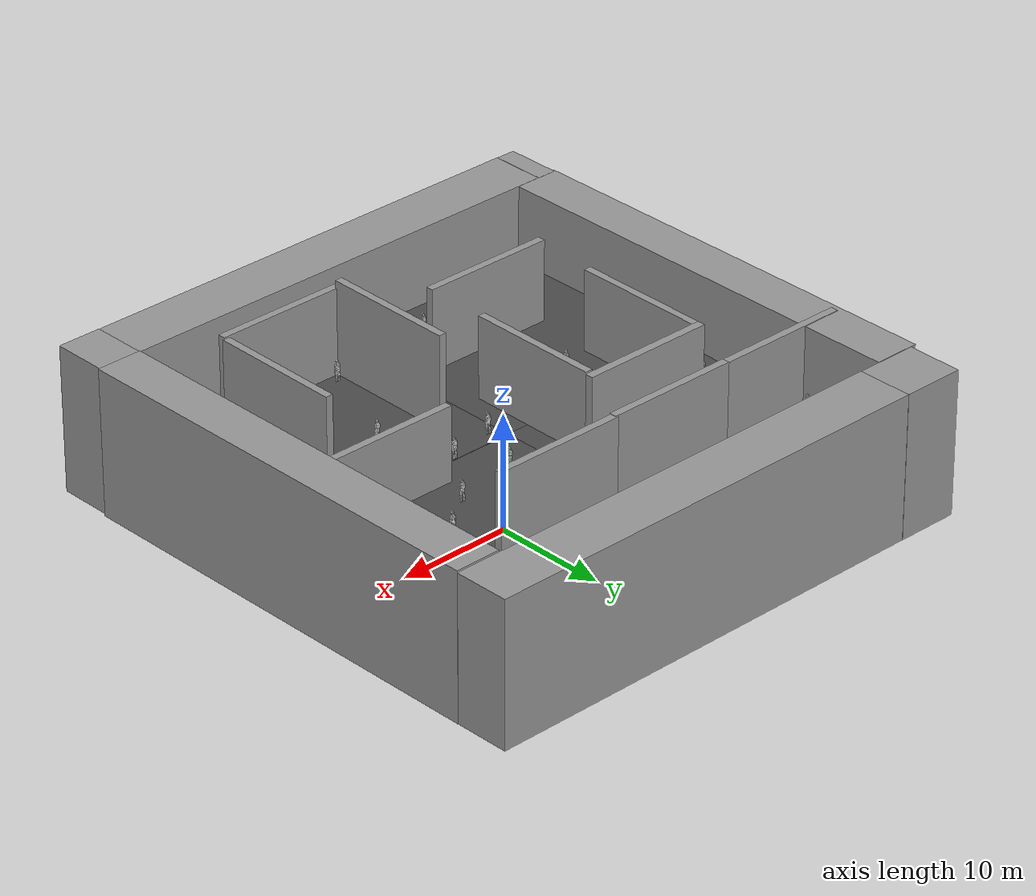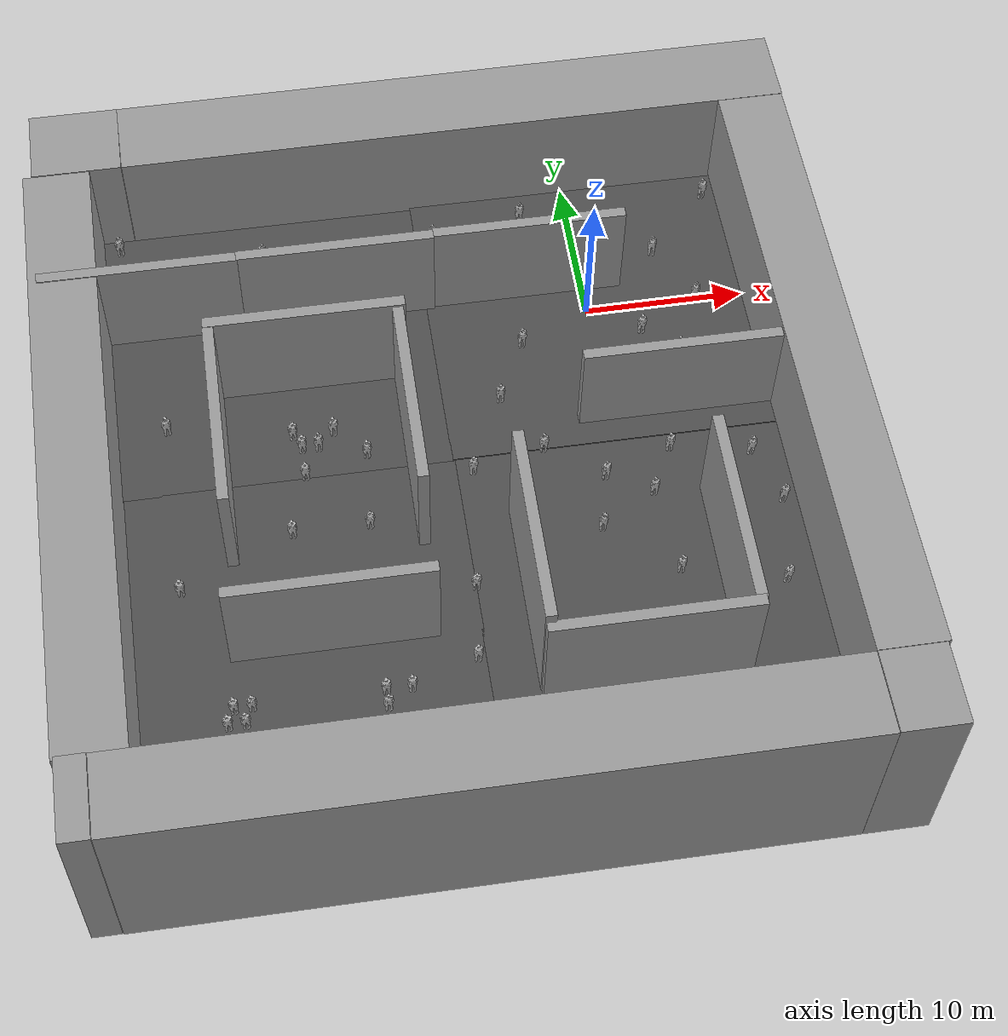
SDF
<?xml version='1.0'?>
<sdf version='1.6'>
  <model name='indoor'>
    <link name='link'>
      <pose frame=''>0 0 0 0 -0 0</pose>
      <self_collide>0</self_collide>
      <kinematic>0</kinematic>
      <visual name='visual'>
        <cast_shadows>0</cast_shadows>
        <geometry>
          <box>
            <size>20 20 0.1</size>
          </box>
        </geometry>
        <material>
          <script>
            <uri>model://asphalt_plane/materials/scripts</uri>
            <uri>model://asphalt_plane/materials/textures</uri>
            <name>vrc/asphalt</name>
          </script>
          <ambient>0.5 0.5 0.5 1</ambient>
          <diffuse>0.5 0.5 0.5 1</diffuse>
          <specular>0.2 0.2 0.2 1</specular>
          <emissive>0 0 0 1</emissive>
        </material>
        <pose frame=''>0 0 0 0 -0 0</pose>
        <transparency>0</transparency>
      </visual>
      <collision name='collision'>
        <laser_retro>0</laser_retro>
        <max_contacts>10</max_contacts>
        <pose frame=''>0 0 0 0 -0 0</pose>
        <geometry>
          <box>
            <size>20 20 0.1</size>
          </box>
        </geometry>
        <surface>
          <friction>
            <ode>
              <mu>1</mu>
              <mu2>1</mu2>
              <fdir1>0 0 0</fdir1>
              <slip1>0</slip1>
              <slip2>0</slip2>
            </ode>
            <torsional>
              <coefficient>1</coefficient>
              <patch_radius>0</patch_radius>
              <surface_radius>0</surface_radius>
              <use_patch_radius>1</use_patch_radius>
              <ode>
                <slip>0</slip>
              </ode>
            </torsional>
          </friction>
          <bounce>
            <restitution_coefficient>0</restitution_coefficient>
            <threshold>1e+06</threshold>
          </bounce>
          <contact>
            <collide_without_contact>0</collide_without_contact>
            <collide_without_contact_bitmask>1</collide_without_contact_bitmask>
            <collide_bitmask>1</collide_bitmask>
            <ode>
              <soft_cfm>0</soft_cfm>
              <soft_erp>0.2</soft_erp>
              <kp>1e+13</kp>
              <kd>1</kd>
              <max_vel>0.01</max_vel>
              <min_depth>0</min_depth>
            </ode>
            <bullet>
              <split_impulse>1</split_impulse>
              <split_impulse_penetration_threshold>-0.01</split_impulse_penetration_threshold>
              <soft_cfm>0</soft_cfm>
              <soft_erp>0.2</soft_erp>
              <kp>1e+13</kp>
              <kd>1</kd>
            </bullet>
          </contact>
        </surface>
      </collision>
    </link>
    <link name='link_0'>
      <pose frame=''>-3.5958 2.04635 0.5 0 -0 0</pose>
      <inertial>
        <mass>104.933</mass>
        <inertia>
          <ixx>1481.69</ixx>
          <ixy>0</ixy>
          <ixz>0</ixz>
          <iyy>2754.45</iyy>
          <iyz>0</iyz>
          <izz>1280.56</izz>
        </inertia>
        <pose frame=''>0 0 0 0 -0 0</pose>
      </inertial>
      <self_collide>0</self_collide>
      <kinematic>0</kinematic>
      <visual name='visual'>
        <pose frame=''>0 0 0 0 -0 0</pose>
        <geometry>
          <box>
            <size>12.0829 0.668042 12.9999</size>
          </box>
        </geometry>
        <material>
          <lighting>1</lighting>
          <script>
            <uri>file://media/materials/scripts/gazebo.material</uri>
            <name>Gazebo/Grey</name>
          </script>
          <ambient>0.3 0.3 0.3 1</ambient>
          <diffuse>0.7 0.7 0.7 1</diffuse>
          <specular>0.01 0.01 0.01 1</specular>
          <emissive>0 0 0 1</emissive>
        </material>
        <cast_shadows>1</cast_shadows>
        <transparency>0</transparency>
      </visual>
      <collision name='collision'>
        <laser_retro>0</laser_retro>
        <max_contacts>10</max_contacts>
        <pose frame=''>0 0 0 0 -0 0</pose>
        <geometry>
          <box>
            <size>12.0829 0.668042 12.9999</size>
          </box>
        </geometry>
        <surface>
          <friction>
            <ode>
              <mu>1</mu>
              <mu2>1</mu2>
              <fdir1>0 0 0</fdir1>
              <slip1>0</slip1>
              <slip2>0</slip2>
            </ode>
            <torsional>
              <coefficient>1</coefficient>
              <patch_radius>0</patch_radius>
              <surface_radius>0</surface_radius>
              <use_patch_radius>1</use_patch_radius>
              <ode>
                <slip>0</slip>
              </ode>
            </torsional>
          </friction>
          <bounce>
            <restitution_coefficient>0</restitution_coefficient>
            <threshold>1e+06</threshold>
          </bounce>
          <contact>
            <collide_without_contact>0</collide_without_contact>
            <collide_without_contact_bitmask>1</collide_without_contact_bitmask>
            <collide_bitmask>1</collide_bitmask>
            <ode>
              <soft_cfm>0</soft_cfm>
              <soft_erp>0.2</soft_erp>
              <kp>1e+13</kp>
              <kd>1</kd>
              <max_vel>0.01</max_vel>
              <min_depth>0</min_depth>
            </ode>
            <bullet>
              <split_impulse>1</split_impulse>
              <split_impulse_penetration_threshold>-0.01</split_impulse_penetration_threshold>
              <soft_cfm>0</soft_cfm>
              <soft_erp>0.2</soft_erp>
              <kp>1e+13</kp>
              <kd>1</kd>
            </bullet>
          </contact>
        </surface>
      </collision>
    </link>
    <link name='link_0_clone'>
      <pose frame=''>-17.9053 -3.11934 0.5 0 -0 0</pose>
      <inertial>
        <mass>118.443</mass>
        <inertia>
          <ixx>1866.46</ixx>
          <ixy>0</ixy>
          <ixz>0</ixz>
          <iyy>3302.46</iyy>
          <iyz>0</iyz>
          <izz>1446.06</izz>
        </inertia>
        <pose frame=''>0 0 0 0 -0 0</pose>
      </inertial>
      <self_collide>0</self_collide>
      <kinematic>0</kinematic>
      <visual name='visual'>
        <pose frame=''>0 0 0 0 -0 0</pose>
        <geometry>
          <box>
            <size>12.0829 0.713863 13.7328</size>
          </box>
        </geometry>
        <material>
          <lighting>1</lighting>
          <script>
            <uri>file://media/materials/scripts/gazebo.material</uri>
            <name>Gazebo/Grey</name>
          </script>
          <ambient>0.3 0.3 0.3 1</ambient>
          <diffuse>0.7 0.7 0.7 1</diffuse>
          <specular>0.01 0.01 0.01 1</specular>
          <emissive>0 0 0 1</emissive>
          <shader type='pixel'/>
        </material>
        <cast_shadows>1</cast_shadows>
        <transparency>0</transparency>
      </visual>
      <collision name='collision'>
        <laser_retro>0</laser_retro>
        <max_contacts>10</max_contacts>
        <pose frame=''>0 0 0 0 -0 0</pose>
        <geometry>
          <box>
            <size>12.0829 0.713863 13.7328</size>
          </box>
        </geometry>
        <surface>
          <friction>
            <ode>
              <mu>1</mu>
              <mu2>1</mu2>
              <fdir1>0 0 0</fdir1>
              <slip1>0</slip1>
              <slip2>0</slip2>
            </ode>
            <torsional>
              <coefficient>1</coefficient>
              <patch_radius>0</patch_radius>
              <surface_radius>0</surface_radius>
              <use_patch_radius>1</use_patch_radius>
              <ode>
                <slip>0</slip>
              </ode>
            </torsional>
          </friction>
          <bounce>
            <restitution_coefficient>0</restitution_coefficient>
            <threshold>1e+06</threshold>
          </bounce>
          <contact>
            <collide_without_contact>0</collide_without_contact>
            <collide_without_contact_bitmask>1</collide_without_contact_bitmask>
            <collide_bitmask>1</collide_bitmask>
            <ode>
              <soft_cfm>0</soft_cfm>
              <soft_erp>0.2</soft_erp>
              <kp>1e+13</kp>
              <kd>1</kd>
              <max_vel>0.01</max_vel>
              <min_depth>0</min_depth>
            </ode>
            <bullet>
              <split_impulse>1</split_impulse>
              <split_impulse_penetration_threshold>-0.01</split_impulse_penetration_threshold>
              <soft_cfm>0</soft_cfm>
              <soft_erp>0.2</soft_erp>
              <kp>1e+13</kp>
              <kd>1</kd>
            </bullet>
          </contact>
        </surface>
      </collision>
    </link>
    <link name='link_0_clone_0'>
      <pose frame=''>-6.91392 12.6282 0.5 0 -0 0.0064</pose>
      <inertial>
        <mass>2670.05</mass>
        <inertia>
          <ixx>42334.8</ixx>
          <ixy>0</ixy>
          <ixz>0</ixz>
          <iyy>432222</iyy>
          <iyz>0</iyz>
          <izz>400641</izz>
        </inertia>
        <pose frame=''>0 0 0 0 -0 0</pose>
      </inertial>
      <self_collide>0</self_collide>
      <kinematic>0</kinematic>
      <visual name='visual'>
        <pose frame=''>0 0 0 0 -0 0</pose>
        <geometry>
          <box>
            <size>42.1476 4.91564 12.8876</size>
          </box>
        </geometry>
        <material>
          <lighting>1</lighting>
          <script>
            <uri>file://media/materials/scripts/gazebo.material</uri>
            <name>Gazebo/Grey</name>
          </script>
          <ambient>0.3 0.3 0.3 1</ambient>
          <diffuse>0.7 0.7 0.7 1</diffuse>
          <specular>0.01 0.01 0.01 1</specular>
          <emissive>0 0 0 1</emissive>
          <shader type='pixel'/>
        </material>
        <cast_shadows>1</cast_shadows>
        <transparency>0</transparency>
      </visual>
      <collision name='collision'>
        <laser_retro>0</laser_retro>
        <max_contacts>10</max_contacts>
        <pose frame=''>0 0 0 0 -0 0</pose>
        <geometry>
          <box>
            <size>42.1476 4.91564 12.8876</size>
          </box>
        </geometry>
        <surface>
          <friction>
            <ode>
              <mu>1</mu>
              <mu2>1</mu2>
              <fdir1>0 0 0</fdir1>
              <slip1>0</slip1>
              <slip2>0</slip2>
            </ode>
            <torsional>
              <coefficient>1</coefficient>
              <patch_radius>0</patch_radius>
              <surface_radius>0</surface_radius>
              <use_patch_radius>1</use_patch_radius>
              <ode>
                <slip>0</slip>
              </ode>
            </torsional>
          </friction>
          <bounce>
            <restitution_coefficient>0</restitution_coefficient>
            <threshold>1e+06</threshold>
          </bounce>
          <contact>
            <collide_without_contact>0</collide_without_contact>
            <collide_without_contact_bitmask>1</collide_without_contact_bitmask>
            <collide_bitmask>1</collide_bitmask>
            <ode>
              <soft_cfm>0</soft_cfm>
              <soft_erp>0.2</soft_erp>
              <kp>1e+13</kp>
              <kd>1</kd>
              <max_vel>0.01</max_vel>
              <min_depth>0</min_depth>
            </ode>
            <bullet>
              <split_impulse>1</split_impulse>
              <split_impulse_penetration_threshold>-0.01</split_impulse_penetration_threshold>
              <soft_cfm>0</soft_cfm>
              <soft_erp>0.2</soft_erp>
              <kp>1e+13</kp>
              <kd>1</kd>
            </bullet>
          </contact>
        </surface>
      </collision>
    </link>
    <link name='link_0_clone_0_clone_0'>
      <pose frame=''>4.09467 -8.11934 0.5 0 -0 0</pose>
      <inertial>
        <mass>100.418</mass>
        <inertia>
          <ixx>1298.85</ixx>
          <ixy>0</ixy>
          <ixz>0</ixz>
          <iyy>2516.84</iyy>
          <iyz>0</iyz>
          <izz>1225.46</izz>
        </inertia>
        <pose frame=''>0 0 0 0 -0 0</pose>
      </inertial>
      <self_collide>0</self_collide>
      <kinematic>0</kinematic>
      <visual name='visual'>
        <pose frame=''>0 0 0 0 -0 0</pose>
        <geometry>
          <box>
            <size>12.0829 0.668042 12.4405</size>
          </box>
        </geometry>
        <material>
          <lighting>1</lighting>
          <script>
            <uri>file://media/materials/scripts/gazebo.material</uri>
            <name>Gazebo/Grey</name>
          </script>
          <ambient>0.3 0.3 0.3 1</ambient>
          <diffuse>0.7 0.7 0.7 1</diffuse>
          <specular>0.01 0.01 0.01 1</specular>
          <emissive>0 0 0 1</emissive>
          <shader type='pixel'/>
        </material>
        <cast_shadows>1</cast_shadows>
        <transparency>0</transparency>
      </visual>
      <collision name='collision'>
        <laser_retro>0</laser_retro>
        <max_contacts>10</max_contacts>
        <pose frame=''>0 0 0 0 -0 0</pose>
        <geometry>
          <box>
            <size>12.0829 0.668042 12.4405</size>
          </box>
        </geometry>
        <surface>
          <friction>
            <ode>
              <mu>1</mu>
              <mu2>1</mu2>
              <fdir1>0 0 0</fdir1>
              <slip1>0</slip1>
              <slip2>0</slip2>
            </ode>
            <torsional>
              <coefficient>1</coefficient>
              <patch_radius>0</patch_radius>
              <surface_radius>0</surface_radius>
              <use_patch_radius>1</use_patch_radius>
              <ode>
                <slip>0</slip>
              </ode>
            </torsional>
          </friction>
          <bounce>
            <restitution_coefficient>0</restitution_coefficient>
            <threshold>1e+06</threshold>
          </bounce>
          <contact>
            <collide_without_contact>0</collide_without_contact>
            <collide_without_contact_bitmask>1</collide_without_contact_bitmask>
            <collide_bitmask>1</collide_bitmask>
            <ode>
              <soft_cfm>0</soft_cfm>
              <soft_erp>0.2</soft_erp>
              <kp>1e+13</kp>
              <kd>1</kd>
              <max_vel>0.01</max_vel>
              <min_depth>0</min_depth>
            </ode>
            <bullet>
              <split_impulse>1</split_impulse>
              <split_impulse_penetration_threshold>-0.01</split_impulse_penetration_threshold>
              <soft_cfm>0</soft_cfm>
              <soft_erp>0.2</soft_erp>
              <kp>1e+13</kp>
              <kd>1</kd>
            </bullet>
          </contact>
        </surface>
      </collision>
    </link>
    <link name='link_0_clone_0_clone_1'>
      <pose frame=''>-18.4124 -21.5717 0.5 0 -0 0</pose>
      <inertial>
        <mass>111.127</mass>
        <inertia>
          <ixx>1759.36</ixx>
          <ixy>0</ixy>
          <ixz>0</ixz>
          <iyy>3107.24</iyy>
          <iyz>0</iyz>
          <izz>1356.15</izz>
        </inertia>
        <pose frame=''>0 0 0 0 -0 0</pose>
      </inertial>
      <self_collide>0</self_collide>
      <kinematic>0</kinematic>
      <visual name='visual'>
        <pose frame=''>0 0 0 0 -0 0</pose>
        <geometry>
          <box>
            <size>12.0829 0.668042 13.7672</size>
          </box>
        </geometry>
        <material>
          <lighting>1</lighting>
          <script>
            <uri>file://media/materials/scripts/gazebo.material</uri>
            <name>Gazebo/Grey</name>
          </script>
          <ambient>0.3 0.3 0.3 1</ambient>
          <diffuse>0.7 0.7 0.7 1</diffuse>
          <specular>0.01 0.01 0.01 1</specular>
          <emissive>0 0 0 1</emissive>
          <shader type='pixel'/>
        </material>
        <cast_shadows>1</cast_shadows>
        <transparency>0</transparency>
      </visual>
      <collision name='collision'>
        <laser_retro>0</laser_retro>
        <max_contacts>10</max_contacts>
        <pose frame=''>0 0 0 0 -0 0</pose>
        <geometry>
          <box>
            <size>12.0829 0.668042 13.7672</size>
          </box>
        </geometry>
        <surface>
          <friction>
            <ode>
              <mu>1</mu>
              <mu2>1</mu2>
              <fdir1>0 0 0</fdir1>
              <slip1>0</slip1>
              <slip2>0</slip2>
            </ode>
            <torsional>
              <coefficient>1</coefficient>
              <patch_radius>0</patch_radius>
              <surface_radius>0</surface_radius>
              <use_patch_radius>1</use_patch_radius>
              <ode>
                <slip>0</slip>
              </ode>
            </torsional>
          </friction>
          <bounce>
            <restitution_coefficient>0</restitution_coefficient>
            <threshold>1e+06</threshold>
          </bounce>
          <contact>
            <collide_without_contact>0</collide_without_contact>
            <collide_without_contact_bitmask>1</collide_without_contact_bitmask>
            <collide_bitmask>1</collide_bitmask>
            <ode>
              <soft_cfm>0</soft_cfm>
              <soft_erp>0.2</soft_erp>
              <kp>1e+13</kp>
              <kd>1</kd>
              <max_vel>0.01</max_vel>
              <min_depth>0</min_depth>
            </ode>
            <bullet>
              <split_impulse>1</split_impulse>
              <split_impulse_penetration_threshold>-0.01</split_impulse_penetration_threshold>
              <soft_cfm>0</soft_cfm>
              <soft_erp>0.2</soft_erp>
              <kp>1e+13</kp>
              <kd>1</kd>
            </bullet>
          </contact>
        </surface>
      </collision>
    </link>
    <link name='link_0_clone_0_clone_2'>
      <pose frame=''>-1.17788 -26.3842 0.5 0 -0 0</pose>
      <inertial>
        <mass>117.056</mass>
        <inertia>
          <ixx>2055.8</ixx>
          <ixy>0</ixy>
          <ixz>0</ixz>
          <iyy>3475.6</iyy>
          <iyz>0</iyz>
          <izz>1428.51</izz>
        </inertia>
        <pose frame=''>0 0 0 0 -0 0</pose>
      </inertial>
      <self_collide>0</self_collide>
      <kinematic>0</kinematic>
      <visual name='visual'>
        <pose frame=''>0 0 0 0 -0 0</pose>
        <geometry>
          <box>
            <size>12.0829 0.668042 14.5018</size>
          </box>
        </geometry>
        <material>
          <lighting>1</lighting>
          <script>
            <uri>file://media/materials/scripts/gazebo.material</uri>
            <name>Gazebo/Grey</name>
          </script>
          <ambient>0.3 0.3 0.3 1</ambient>
          <diffuse>0.7 0.7 0.7 1</diffuse>
          <specular>0.01 0.01 0.01 1</specular>
          <emissive>0 0 0 1</emissive>
          <shader type='pixel'/>
        </material>
        <cast_shadows>1</cast_shadows>
        <transparency>0</transparency>
      </visual>
      <collision name='collision'>
        <laser_retro>0</laser_retro>
        <max_contacts>10</max_contacts>
        <pose frame=''>0 0 0 0 -0 0</pose>
        <geometry>
          <box>
            <size>12.0829 0.668042 14.5018</size>
          </box>
        </geometry>
        <surface>
          <friction>
            <ode>
              <mu>1</mu>
              <mu2>1</mu2>
              <fdir1>0 0 0</fdir1>
              <slip1>0</slip1>
              <slip2>0</slip2>
            </ode>
            <torsional>
              <coefficient>1</coefficient>
              <patch_radius>0</patch_radius>
              <surface_radius>0</surface_radius>
              <use_patch_radius>1</use_patch_radius>
              <ode>
                <slip>0</slip>
              </ode>
            </torsional>
          </friction>
          <bounce>
            <restitution_coefficient>0</restitution_coefficient>
            <threshold>1e+06</threshold>
          </bounce>
          <contact>
            <collide_without_contact>0</collide_without_contact>
            <collide_without_contact_bitmask>1</collide_without_contact_bitmask>
            <collide_bitmask>1</collide_bitmask>
            <ode>
              <soft_cfm>0</soft_cfm>
              <soft_erp>0.2</soft_erp>
              <kp>1e+13</kp>
              <kd>1</kd>
              <max_vel>0.01</max_vel>
              <min_depth>0</min_depth>
            </ode>
            <bullet>
              <split_impulse>1</split_impulse>
              <split_impulse_penetration_threshold>-0.01</split_impulse_penetration_threshold>
              <soft_cfm>0</soft_cfm>
              <soft_erp>0.2</soft_erp>
              <kp>1e+13</kp>
              <kd>1</kd>
            </bullet>
          </contact>
        </surface>
      </collision>
    </link>
    <link name='link_0_clone_0_clone_3'>
      <pose frame=''>-30.7681 12.5167 0.5 0 -0 0</pose>
      <inertial>
        <mass>350.589</mass>
        <inertia>
          <ixx>5546.34</ixx>
          <ixy>0</ixy>
          <ixz>0</ixz>
          <iyy>5737.39</iyy>
          <iyz>0</iyz>
          <izz>1603.12</izz>
        </inertia>
        <pose frame=''>0 0 0 0 -0 0</pose>
      </inertial>
      <self_collide>0</self_collide>
      <kinematic>0</kinematic>
      <visual name='visual'>
        <pose frame=''>0 0 0 0 -0 0</pose>
        <geometry>
          <box>
            <size>5.54125 4.91564 12.8711</size>
          </box>
        </geometry>
        <material>
          <lighting>1</lighting>
          <script>
            <uri>file://media/materials/scripts/gazebo.material</uri>
            <name>Gazebo/Grey</name>
          </script>
          <ambient>0.3 0.3 0.3 1</ambient>
          <diffuse>0.7 0.7 0.7 1</diffuse>
          <specular>0.01 0.01 0.01 1</specular>
          <emissive>0 0 0 1</emissive>
          <shader type='pixel'/>
        </material>
        <cast_shadows>1</cast_shadows>
        <transparency>0</transparency>
      </visual>
      <collision name='collision'>
        <laser_retro>0</laser_retro>
        <max_contacts>10</max_contacts>
        <pose frame=''>0 0 0 0 -0 0</pose>
        <geometry>
          <box>
            <size>5.54125 4.91564 12.8711</size>
          </box>
        </geometry>
        <surface>
          <friction>
            <ode>
              <mu>1</mu>
              <mu2>1</mu2>
              <fdir1>0 0 0</fdir1>
              <slip1>0</slip1>
              <slip2>0</slip2>
            </ode>
            <torsional>
              <coefficient>1</coefficient>
              <patch_radius>0</patch_radius>
              <surface_radius>0</surface_radius>
              <use_patch_radius>1</use_patch_radius>
              <ode>
                <slip>0</slip>
              </ode>
            </torsional>
          </friction>
          <bounce>
            <restitution_coefficient>0</restitution_coefficient>
            <threshold>1e+06</threshold>
          </bounce>
          <contact>
            <collide_without_contact>0</collide_without_contact>
            <collide_without_contact_bitmask>1</collide_without_contact_bitmask>
            <collide_bitmask>1</collide_bitmask>
            <ode>
              <soft_cfm>0</soft_cfm>
              <soft_erp>0.2</soft_erp>
              <kp>1e+13</kp>
              <kd>1</kd>
              <max_vel>0.01</max_vel>
              <min_depth>0</min_depth>
            </ode>
            <bullet>
              <split_impulse>1</split_impulse>
              <split_impulse_penetration_threshold>-0.01</split_impulse_penetration_threshold>
              <soft_cfm>0</soft_cfm>
              <soft_erp>0.2</soft_erp>
              <kp>1e+13</kp>
              <kd>1</kd>
            </bullet>
          </contact>
        </surface>
      </collision>
    </link>
    <link name='link_0_clone_0_clone_3_clone'>
      <pose frame=''>-32.9522 -32.3454 0.5 0 -0 0</pose>
      <inertial>
        <mass>110.757</mass>
        <inertia>
          <ixx>1757.01</ixx>
          <ixy>0</ixy>
          <ixz>0</ixz>
          <iyy>1562.16</iyy>
          <iyz>0</iyz>
          <izz>251.243</izz>
        </inertia>
        <pose frame=''>0 0 0 0 -0 0</pose>
      </inertial>
      <self_collide>0</self_collide>
      <kinematic>0</kinematic>
      <visual name='visual'>
        <pose frame=''>0 0 0 0 -0 0</pose>
        <geometry>
          <box>
            <size>1.74782 4.91564 12.8914</size>
          </box>
        </geometry>
        <material>
          <lighting>1</lighting>
          <script>
            <uri>file://media/materials/scripts/gazebo.material</uri>
            <name>Gazebo/Grey</name>
          </script>
          <ambient>0.3 0.3 0.3 1</ambient>
          <diffuse>0.7 0.7 0.7 1</diffuse>
          <specular>0.01 0.01 0.01 1</specular>
          <emissive>0 0 0 1</emissive>
          <shader type='pixel'/>
        </material>
        <cast_shadows>1</cast_shadows>
        <transparency>0</transparency>
      </visual>
      <collision name='collision'>
        <laser_retro>0</laser_retro>
        <max_contacts>10</max_contacts>
        <pose frame=''>0 0 0 0 -0 0</pose>
        <geometry>
          <box>
            <size>1.74782 4.91564 12.8914</size>
          </box>
        </geometry>
        <surface>
          <friction>
            <ode>
              <mu>1</mu>
              <mu2>1</mu2>
              <fdir1>0 0 0</fdir1>
              <slip1>0</slip1>
              <slip2>0</slip2>
            </ode>
            <torsional>
              <coefficient>1</coefficient>
              <patch_radius>0</patch_radius>
              <surface_radius>0</surface_radius>
              <use_patch_radius>1</use_patch_radius>
              <ode>
                <slip>0</slip>
              </ode>
            </torsional>
          </friction>
          <bounce>
            <restitution_coefficient>0</restitution_coefficient>
            <threshold>1e+06</threshold>
          </bounce>
          <contact>
            <collide_without_contact>0</collide_without_contact>
            <collide_without_contact_bitmask>1</collide_without_contact_bitmask>
            <collide_bitmask>1</collide_bitmask>
            <ode>
              <soft_cfm>0</soft_cfm>
              <soft_erp>0.2</soft_erp>
              <kp>1e+13</kp>
              <kd>1</kd>
              <max_vel>0.01</max_vel>
              <min_depth>0</min_depth>
            </ode>
            <bullet>
              <split_impulse>1</split_impulse>
              <split_impulse_penetration_threshold>-0.01</split_impulse_penetration_threshold>
              <soft_cfm>0</soft_cfm>
              <soft_erp>0.2</soft_erp>
              <kp>1e+13</kp>
              <kd>1</kd>
            </bullet>
          </contact>
        </surface>
      </collision>
    </link>
    <link name='link_0_clone_0_clone_3_clone_clone'>
      <pose frame=''>12.0862 -32.3668 0.5 0 -0 0</pose>
      <inertial>
        <mass>249.83</mass>
        <inertia>
          <ixx>4011.02</ixx>
          <ixy>0</ixy>
          <ixz>0</ixz>
          <iyy>3827.09</iyy>
          <iyz>0</iyz>
          <izz>822.306</izz>
        </inertia>
        <pose frame=''>0 0 0 0 -0 0</pose>
      </inertial>
      <self_collide>0</self_collide>
      <kinematic>0</kinematic>
      <visual name='visual'>
        <pose frame=''>0 0 0 0 -0 0</pose>
        <geometry>
          <box>
            <size>3.91552 4.91564 12.9802</size>
          </box>
        </geometry>
        <material>
          <lighting>1</lighting>
          <script>
            <uri>file://media/materials/scripts/gazebo.material</uri>
            <name>Gazebo/Grey</name>
          </script>
          <ambient>0.3 0.3 0.3 1</ambient>
          <diffuse>0.7 0.7 0.7 1</diffuse>
          <specular>0.01 0.01 0.01 1</specular>
          <emissive>0 0 0 1</emissive>
          <shader type='pixel'/>
        </material>
        <cast_shadows>1</cast_shadows>
        <transparency>0</transparency>
      </visual>
      <collision name='collision'>
        <laser_retro>0</laser_retro>
        <max_contacts>10</max_contacts>
        <pose frame=''>0 0 0 0 -0 0</pose>
        <geometry>
          <box>
            <size>3.91552 4.91564 12.9802</size>
          </box>
        </geometry>
        <surface>
          <friction>
            <ode>
              <mu>1</mu>
              <mu2>1</mu2>
              <fdir1>0 0 0</fdir1>
              <slip1>0</slip1>
              <slip2>0</slip2>
            </ode>
            <torsional>
              <coefficient>1</coefficient>
              <patch_radius>0</patch_radius>
              <surface_radius>0</surface_radius>
              <use_patch_radius>1</use_patch_radius>
              <ode>
                <slip>0</slip>
              </ode>
            </torsional>
          </friction>
          <bounce>
            <restitution_coefficient>0</restitution_coefficient>
            <threshold>1e+06</threshold>
          </bounce>
          <contact>
            <collide_without_contact>0</collide_without_contact>
            <collide_without_contact_bitmask>1</collide_without_contact_bitmask>
            <collide_bitmask>1</collide_bitmask>
            <ode>
              <soft_cfm>0</soft_cfm>
              <soft_erp>0.2</soft_erp>
              <kp>1e+13</kp>
              <kd>1</kd>
              <max_vel>0.01</max_vel>
              <min_depth>0</min_depth>
            </ode>
            <bullet>
              <split_impulse>1</split_impulse>
              <split_impulse_penetration_threshold>-0.01</split_impulse_penetration_threshold>
              <soft_cfm>0</soft_cfm>
              <soft_erp>0.2</soft_erp>
              <kp>1e+13</kp>
              <kd>1</kd>
            </bullet>
          </contact>
        </surface>
      </collision>
    </link>
    <link name='link_0_clone_0_clone_4'>
      <pose frame=''>-10.9678 -32.384 0.5 0 -0 0</pose>
      <inertial>
        <mass>2672.62</mass>
        <inertia>
          <ixx>42446.8</ixx>
          <ixy>0</ixy>
          <ixz>0</ixz>
          <iyy>432709</iyy>
          <iyz>0</iyz>
          <izz>401026</izz>
        </inertia>
        <pose frame=''>0 0 0 0 -0 0</pose>
      </inertial>
      <self_collide>0</self_collide>
      <kinematic>0</kinematic>
      <visual name='visual'>
        <pose frame=''>0 0 0 0 -0 0</pose>
        <geometry>
          <box>
            <size>42.1476 4.91564 12.9</size>
          </box>
        </geometry>
        <material>
          <lighting>1</lighting>
          <script>
            <uri>file://media/materials/scripts/gazebo.material</uri>
            <name>Gazebo/Grey</name>
          </script>
          <ambient>0.3 0.3 0.3 1</ambient>
          <diffuse>0.7 0.7 0.7 1</diffuse>
          <specular>0.01 0.01 0.01 1</specular>
          <emissive>0 0 0 1</emissive>
          <shader type='pixel'/>
        </material>
        <cast_shadows>1</cast_shadows>
        <transparency>0</transparency>
      </visual>
      <collision name='collision'>
        <laser_retro>0</laser_retro>
        <max_contacts>10</max_contacts>
        <pose frame=''>0 0 0 0 -0 0</pose>
        <geometry>
          <box>
            <size>42.1476 4.91564 12.9</size>
          </box>
        </geometry>
        <surface>
          <friction>
            <ode>
              <mu>1</mu>
              <mu2>1</mu2>
              <fdir1>0 0 0</fdir1>
              <slip1>0</slip1>
              <slip2>0</slip2>
            </ode>
            <torsional>
              <coefficient>1</coefficient>
              <patch_radius>0</patch_radius>
              <surface_radius>0</surface_radius>
              <use_patch_radius>1</use_patch_radius>
              <ode>
                <slip>0</slip>
              </ode>
            </torsional>
          </friction>
          <bounce>
            <restitution_coefficient>0</restitution_coefficient>
            <threshold>1e+06</threshold>
          </bounce>
          <contact>
            <collide_without_contact>0</collide_without_contact>
            <collide_without_contact_bitmask>1</collide_without_contact_bitmask>
            <collide_bitmask>1</collide_bitmask>
            <ode>
              <soft_cfm>0</soft_cfm>
              <soft_erp>0.2</soft_erp>
              <kp>1e+13</kp>
              <kd>1</kd>
              <max_vel>0.01</max_vel>
              <min_depth>0</min_depth>
            </ode>
            <bullet>
              <split_impulse>1</split_impulse>
              <split_impulse_penetration_threshold>-0.01</split_impulse_penetration_threshold>
              <soft_cfm>0</soft_cfm>
              <soft_erp>0.2</soft_erp>
              <kp>1e+13</kp>
              <kd>1</kd>
            </bullet>
          </contact>
        </surface>
      </collision>
    </link>
    <link name='link_0_clone_0_clone_clone'>
      <pose frame=''>12.0974 -9.86857 0.5 0 0 -1.56777</pose>
      <inertial>
        <mass>2161.3</mass>
        <inertia>
          <ixx>33855.1</ixx>
          <ixy>0</ixy>
          <ixz>0</ixz>
          <iyy>320569</iyy>
          <iyz>0</iyz>
          <izz>292832</izz>
        </inertia>
        <pose frame=''>0 0 0 0 -0 0</pose>
      </inertial>
      <self_collide>0</self_collide>
      <kinematic>0</kinematic>
      <visual name='visual'>
        <pose frame=''>0 0 0 0 -0 0</pose>
        <geometry>
          <box>
            <size>40.1108 4.1207 13.0764</size>
          </box>
        </geometry>
        <material>
          <lighting>1</lighting>
          <script>
            <uri>file://media/materials/scripts/gazebo.material</uri>
            <name>Gazebo/Grey</name>
          </script>
          <ambient>0.3 0.3 0.3 1</ambient>
          <diffuse>0.7 0.7 0.7 1</diffuse>
          <specular>0.01 0.01 0.01 1</specular>
          <emissive>0 0 0 1</emissive>
          <shader type='pixel'/>
        </material>
        <cast_shadows>1</cast_shadows>
        <transparency>0</transparency>
      </visual>
      <collision name='collision'>
        <laser_retro>0</laser_retro>
        <max_contacts>10</max_contacts>
        <pose frame=''>0 0 0 0 -0 0</pose>
        <geometry>
          <box>
            <size>40.1108 4.1207 13.0764</size>
          </box>
        </geometry>
        <surface>
          <friction>
            <ode>
              <mu>1</mu>
              <mu2>1</mu2>
              <fdir1>0 0 0</fdir1>
              <slip1>0</slip1>
              <slip2>0</slip2>
            </ode>
            <torsional>
              <coefficient>1</coefficient>
              <patch_radius>0</patch_radius>
              <surface_radius>0</surface_radius>
              <use_patch_radius>1</use_patch_radius>
              <ode>
                <slip>0</slip>
              </ode>
            </torsional>
          </friction>
          <bounce>
            <restitution_coefficient>0</restitution_coefficient>
            <threshold>1e+06</threshold>
          </bounce>
          <contact>
            <collide_without_contact>0</collide_without_contact>
            <collide_without_contact_bitmask>1</collide_without_contact_bitmask>
            <collide_bitmask>1</collide_bitmask>
            <ode>
              <soft_cfm>0</soft_cfm>
              <soft_erp>0.2</soft_erp>
              <kp>1e+13</kp>
              <kd>1</kd>
              <max_vel>0.01</max_vel>
              <min_depth>0</min_depth>
            </ode>
            <bullet>
              <split_impulse>1</split_impulse>
              <split_impulse_penetration_threshold>-0.01</split_impulse_penetration_threshold>
              <soft_cfm>0</soft_cfm>
              <soft_erp>0.2</soft_erp>
              <kp>1e+13</kp>
              <kd>1</kd>
            </bullet>
          </contact>
        </surface>
      </collision>
    </link>
    <link name='link_0_clone_0_clone_clone_clone'>
      <pose frame=''>-31.9703 -10.059 0.5 0 0 -1.56777</pose>
      <inertial>
        <mass>2126.69</mass>
        <inertia>
          <ixx>32350.5</ixx>
          <ixy>0</ixy>
          <ixz>0</ixz>
          <iyy>314474</iyy>
          <iyz>0</iyz>
          <izz>288144</izz>
        </inertia>
        <pose frame=''>0 0 0 0 -0 0</pose>
      </inertial>
      <self_collide>0</self_collide>
      <kinematic>0</kinematic>
      <visual name='visual'>
        <pose frame=''>0 0 0 0 -0 0</pose>
        <geometry>
          <box>
            <size>40.1108 4.1207 12.867</size>
          </box>
        </geometry>
        <material>
          <lighting>1</lighting>
          <script>
            <uri>file://media/materials/scripts/gazebo.material</uri>
            <name>Gazebo/Grey</name>
          </script>
          <ambient>0.3 0.3 0.3 1</ambient>
          <diffuse>0.7 0.7 0.7 1</diffuse>
          <specular>0.01 0.01 0.01 1</specular>
          <emissive>0 0 0 1</emissive>
          <shader type='pixel'/>
        </material>
        <cast_shadows>1</cast_shadows>
        <transparency>0</transparency>
      </visual>
      <collision name='collision'>
        <laser_retro>0</laser_retro>
        <max_contacts>10</max_contacts>
        <pose frame=''>0 0 0 0 -0 0</pose>
        <geometry>
          <box>
            <size>40.1108 4.1207 12.867</size>
          </box>
        </geometry>
        <surface>
          <friction>
            <ode>
              <mu>1</mu>
              <mu2>1</mu2>
              <fdir1>0 0 0</fdir1>
              <slip1>0</slip1>
              <slip2>0</slip2>
            </ode>
            <torsional>
              <coefficient>1</coefficient>
              <patch_radius>0</patch_radius>
              <surface_radius>0</surface_radius>
              <use_patch_radius>1</use_patch_radius>
              <ode>
                <slip>0</slip>
              </ode>
            </torsional>
          </friction>
          <bounce>
            <restitution_coefficient>0</restitution_coefficient>
            <threshold>1e+06</threshold>
          </bounce>
          <contact>
            <collide_without_contact>0</collide_without_contact>
            <collide_without_contact_bitmask>1</collide_without_contact_bitmask>
            <collide_bitmask>1</collide_bitmask>
            <ode>
              <soft_cfm>0</soft_cfm>
              <soft_erp>0.2</soft_erp>
              <kp>1e+13</kp>
              <kd>1</kd>
              <max_vel>0.01</max_vel>
              <min_depth>0</min_depth>
            </ode>
            <bullet>
              <split_impulse>1</split_impulse>
              <split_impulse_penetration_threshold>-0.01</split_impulse_penetration_threshold>
              <soft_cfm>0</soft_cfm>
              <soft_erp>0.2</soft_erp>
              <kp>1e+13</kp>
              <kd>1</kd>
            </bullet>
          </contact>
        </surface>
      </collision>
    </link>
    <link name='link_0_clone_1'>
      <pose frame=''>-23.6918 -9.52482 0.5 0 0 -1.5784</pose>
      <inertial>
        <mass>110.395</mass>
        <inertia>
          <ixx>1724.88</ixx>
          <ixy>0</ixy>
          <ixz>0</ixz>
          <iyy>3063.88</iyy>
          <iyz>0</iyz>
          <izz>1347.22</izz>
        </inertia>
        <pose frame=''>0 0 0 0 -0 0</pose>
      </inertial>
      <self_collide>0</self_collide>
      <kinematic>0</kinematic>
      <visual name='visual'>
        <pose frame=''>0 0 0 0 -0 0</pose>
        <geometry>
          <box>
            <size>12.0829 0.668042 13.6765</size>
          </box>
        </geometry>
        <material>
          <lighting>1</lighting>
          <script>
            <uri>file://media/materials/scripts/gazebo.material</uri>
            <name>Gazebo/Grey</name>
          </script>
          <ambient>0.3 0.3 0.3 1</ambient>
          <diffuse>0.7 0.7 0.7 1</diffuse>
          <specular>0.01 0.01 0.01 1</specular>
          <emissive>0 0 0 1</emissive>
          <shader type='pixel'/>
        </material>
        <cast_shadows>1</cast_shadows>
        <transparency>0</transparency>
      </visual>
      <collision name='collision'>
        <laser_retro>0</laser_retro>
        <max_contacts>10</max_contacts>
        <pose frame=''>0 0 0 0 -0 0</pose>
        <geometry>
          <box>
            <size>12.0829 0.668042 13.6765</size>
          </box>
        </geometry>
        <surface>
          <friction>
            <ode>
              <mu>1</mu>
              <mu2>1</mu2>
              <fdir1>0 0 0</fdir1>
              <slip1>0</slip1>
              <slip2>0</slip2>
            </ode>
            <torsional>
              <coefficient>1</coefficient>
              <patch_radius>0</patch_radius>
              <surface_radius>0</surface_radius>
              <use_patch_radius>1</use_patch_radius>
              <ode>
                <slip>0</slip>
              </ode>
            </torsional>
          </friction>
          <bounce>
            <restitution_coefficient>0</restitution_coefficient>
            <threshold>1e+06</threshold>
          </bounce>
          <contact>
            <collide_without_contact>0</collide_without_contact>
            <collide_without_contact_bitmask>1</collide_without_contact_bitmask>
            <collide_bitmask>1</collide_bitmask>
            <ode>
              <soft_cfm>0</soft_cfm>
              <soft_erp>0.2</soft_erp>
              <kp>1e+13</kp>
              <kd>1</kd>
              <max_vel>0.01</max_vel>
              <min_depth>0</min_depth>
            </ode>
            <bullet>
              <split_impulse>1</split_impulse>
              <split_impulse_penetration_threshold>-0.01</split_impulse_penetration_threshold>
              <soft_cfm>0</soft_cfm>
              <soft_erp>0.2</soft_erp>
              <kp>1e+13</kp>
              <kd>1</kd>
            </bullet>
          </contact>
        </surface>
      </collision>
    </link>
    <link name='link_0_clone_1_clone'>
      <pose frame=''>-12.4048 -9.66339 0.5 0 0 -1.5784</pose>
      <inertial>
        <mass>111.663</mass>
        <inertia>
          <ixx>1784.93</ixx>
          <ixy>0</ixy>
          <ixz>0</ixz>
          <iyy>3139.32</iyy>
          <iyz>0</iyz>
          <izz>1362.7</izz>
        </inertia>
        <pose frame=''>0 0 0 0 -0 0</pose>
      </inertial>
      <self_collide>0</self_collide>
      <kinematic>0</kinematic>
      <visual name='visual'>
        <pose frame=''>0 0 0 0 -0 0</pose>
        <geometry>
          <box>
            <size>12.0829 0.668042 13.8337</size>
          </box>
        </geometry>
        <material>
          <lighting>1</lighting>
          <script>
            <uri>file://media/materials/scripts/gazebo.material</uri>
            <name>Gazebo/Grey</name>
          </script>
          <ambient>0.3 0.3 0.3 1</ambient>
          <diffuse>0.7 0.7 0.7 1</diffuse>
          <specular>0.01 0.01 0.01 1</specular>
          <emissive>0 0 0 1</emissive>
          <shader type='pixel'/>
        </material>
        <cast_shadows>1</cast_shadows>
        <transparency>0</transparency>
      </visual>
      <collision name='collision'>
        <laser_retro>0</laser_retro>
        <max_contacts>10</max_contacts>
        <pose frame=''>0 0 0 0 -0 0</pose>
        <geometry>
          <box>
            <size>12.0829 0.668042 13.8337</size>
          </box>
        </geometry>
        <surface>
          <friction>
            <ode>
              <mu>1</mu>
              <mu2>1</mu2>
              <fdir1>0 0 0</fdir1>
              <slip1>0</slip1>
              <slip2>0</slip2>
            </ode>
            <torsional>
              <coefficient>1</coefficient>
              <patch_radius>0</patch_radius>
              <surface_radius>0</surface_radius>
              <use_patch_radius>1</use_patch_radius>
              <ode>
                <slip>0</slip>
              </ode>
            </torsional>
          </friction>
          <bounce>
            <restitution_coefficient>0</restitution_coefficient>
            <threshold>1e+06</threshold>
          </bounce>
          <contact>
            <collide_without_contact>0</collide_without_contact>
            <collide_without_contact_bitmask>1</collide_without_contact_bitmask>
            <collide_bitmask>1</collide_bitmask>
            <ode>
              <soft_cfm>0</soft_cfm>
              <soft_erp>0.2</soft_erp>
              <kp>1e+13</kp>
              <kd>1</kd>
              <max_vel>0.01</max_vel>
              <min_depth>0</min_depth>
            </ode>
            <bullet>
              <split_impulse>1</split_impulse>
              <split_impulse_penetration_threshold>-0.01</split_impulse_penetration_threshold>
              <soft_cfm>0</soft_cfm>
              <soft_erp>0.2</soft_erp>
              <kp>1e+13</kp>
              <kd>1</kd>
            </bullet>
          </contact>
        </surface>
      </collision>
    </link>
    <link name='link_0_clone_1_clone_clone'>
      <pose frame=''>-6.90533 -20.1193 0.5 0 0 -1.5784</pose>
      <inertial>
        <mass>128.082</mass>
        <inertia>
          <ixx>2692.23</ixx>
          <ixy>0</ixy>
          <ixz>0</ixz>
          <iyy>4245.77</iyy>
          <iyz>0</iyz>
          <izz>1563.06</izz>
        </inertia>
        <pose frame=''>0 0 0 0 -0 0</pose>
      </inertial>
      <self_collide>0</self_collide>
      <kinematic>0</kinematic>
      <visual name='visual'>
        <pose frame=''>0 0 0 0 -0 0</pose>
        <geometry>
          <box>
            <size>12.0829 0.668042 15.8678</size>
          </box>
        </geometry>
        <material>
          <lighting>1</lighting>
          <script>
            <uri>file://media/materials/scripts/gazebo.material</uri>
            <name>Gazebo/Grey</name>
          </script>
          <ambient>0.3 0.3 0.3 1</ambient>
          <diffuse>0.7 0.7 0.7 1</diffuse>
          <specular>0.01 0.01 0.01 1</specular>
          <emissive>0 0 0 1</emissive>
          <shader type='pixel'/>
        </material>
        <cast_shadows>1</cast_shadows>
        <transparency>0</transparency>
      </visual>
      <collision name='collision'>
        <laser_retro>0</laser_retro>
        <max_contacts>10</max_contacts>
        <pose frame=''>0 0 0 0 -0 0</pose>
        <geometry>
          <box>
            <size>12.0829 0.668042 15.8678</size>
          </box>
        </geometry>
        <surface>
          <friction>
            <ode>
              <mu>1</mu>
              <mu2>1</mu2>
              <fdir1>0 0 0</fdir1>
              <slip1>0</slip1>
              <slip2>0</slip2>
            </ode>
            <torsional>
              <coefficient>1</coefficient>
              <patch_radius>0</patch_radius>
              <surface_radius>0</surface_radius>
              <use_patch_radius>1</use_patch_radius>
              <ode>
                <slip>0</slip>
              </ode>
            </torsional>
          </friction>
          <bounce>
            <restitution_coefficient>0</restitution_coefficient>
            <threshold>1e+06</threshold>
          </bounce>
          <contact>
            <collide_without_contact>0</collide_without_contact>
            <collide_without_contact_bitmask>1</collide_without_contact_bitmask>
            <collide_bitmask>1</collide_bitmask>
            <ode>
              <soft_cfm>0</soft_cfm>
              <soft_erp>0.2</soft_erp>
              <kp>1e+13</kp>
              <kd>1</kd>
              <max_vel>0.01</max_vel>
              <min_depth>0</min_depth>
            </ode>
            <bullet>
              <split_impulse>1</split_impulse>
              <split_impulse_penetration_threshold>-0.01</split_impulse_penetration_threshold>
              <soft_cfm>0</soft_cfm>
              <soft_erp>0.2</soft_erp>
              <kp>1e+13</kp>
              <kd>1</kd>
            </bullet>
          </contact>
        </surface>
      </collision>
    </link>
    <link name='link_0_clone_1_clone_clone_clone'>
      <pose frame=''>4.68945 -20.1193 0.5 0 0 -1.5784</pose>
      <inertial>
        <mass>114.352</mass>
        <inertia>
          <ixx>1916.77</ixx>
          <ixy>0</ixy>
          <ixz>0</ixz>
          <iyy>3303.77</iyy>
          <iyz>0</iyz>
          <izz>1395.5</izz>
        </inertia>
        <pose frame=''>0 0 0 0 -0 0</pose>
      </inertial>
      <self_collide>0</self_collide>
      <kinematic>0</kinematic>
      <visual name='visual'>
        <pose frame=''>0 0 0 0 -0 0</pose>
        <geometry>
          <box>
            <size>12.0829 0.668042 14.1667</size>
          </box>
        </geometry>
        <material>
          <lighting>1</lighting>
          <script>
            <uri>file://media/materials/scripts/gazebo.material</uri>
            <name>Gazebo/Grey</name>
          </script>
          <ambient>0.3 0.3 0.3 1</ambient>
          <diffuse>0.7 0.7 0.7 1</diffuse>
          <specular>0.01 0.01 0.01 1</specular>
          <emissive>0 0 0 1</emissive>
          <shader type='pixel'/>
        </material>
        <cast_shadows>1</cast_shadows>
        <transparency>0</transparency>
      </visual>
      <collision name='collision'>
        <laser_retro>0</laser_retro>
        <max_contacts>10</max_contacts>
        <pose frame=''>0 0 0 0 -0 0</pose>
        <geometry>
          <box>
            <size>12.0829 0.668042 14.1667</size>
          </box>
        </geometry>
        <surface>
          <friction>
            <ode>
              <mu>1</mu>
              <mu2>1</mu2>
              <fdir1>0 0 0</fdir1>
              <slip1>0</slip1>
              <slip2>0</slip2>
            </ode>
            <torsional>
              <coefficient>1</coefficient>
              <patch_radius>0</patch_radius>
              <surface_radius>0</surface_radius>
              <use_patch_radius>1</use_patch_radius>
              <ode>
                <slip>0</slip>
              </ode>
            </torsional>
          </friction>
          <bounce>
            <restitution_coefficient>0</restitution_coefficient>
            <threshold>1e+06</threshold>
          </bounce>
          <contact>
            <collide_without_contact>0</collide_without_contact>
            <collide_without_contact_bitmask>1</collide_without_contact_bitmask>
            <collide_bitmask>1</collide_bitmask>
            <ode>
              <soft_cfm>0</soft_cfm>
              <soft_erp>0.2</soft_erp>
              <kp>1e+13</kp>
              <kd>1</kd>
              <max_vel>0.01</max_vel>
              <min_depth>0</min_depth>
            </ode>
            <bullet>
              <split_impulse>1</split_impulse>
              <split_impulse_penetration_threshold>-0.01</split_impulse_penetration_threshold>
              <soft_cfm>0</soft_cfm>
              <soft_erp>0.2</soft_erp>
              <kp>1e+13</kp>
              <kd>1</kd>
            </bullet>
          </contact>
        </surface>
      </collision>
    </link>
    <link name='link_0_clone_2'>
      <pose frame=''>-15.5128 1.9188 0.5 0 -0 0</pose>
      <inertial>
        <mass>105.543</mass>
        <inertia>
          <ixx>1507.64</ixx>
          <ixy>0</ixy>
          <ixz>0</ixz>
          <iyy>2787.8</iyy>
          <iyz>0</iyz>
          <izz>1288.01</izz>
        </inertia>
        <pose frame=''>0 0 0 0 -0 0</pose>
      </inertial>
      <self_collide>0</self_collide>
      <kinematic>0</kinematic>
      <visual name='visual'>
        <pose frame=''>0 0 0 0 -0 0</pose>
        <geometry>
          <box>
            <size>12.0829 0.668042 13.0755</size>
          </box>
        </geometry>
        <material>
          <lighting>1</lighting>
          <script>
            <uri>file://media/materials/scripts/gazebo.material</uri>
            <name>Gazebo/Grey</name>
          </script>
          <ambient>0.3 0.3 0.3 1</ambient>
          <diffuse>0.7 0.7 0.7 1</diffuse>
          <specular>0.01 0.01 0.01 1</specular>
          <emissive>0 0 0 1</emissive>
          <shader type='pixel'/>
        </material>
        <cast_shadows>1</cast_shadows>
        <transparency>0</transparency>
      </visual>
      <collision name='collision'>
        <laser_retro>0</laser_retro>
        <max_contacts>10</max_contacts>
        <pose frame=''>0 0 0 0 -0 0</pose>
        <geometry>
          <box>
            <size>12.0829 0.668042 13.0755</size>
          </box>
        </geometry>
        <surface>
          <friction>
            <ode>
              <mu>1</mu>
              <mu2>1</mu2>
              <fdir1>0 0 0</fdir1>
              <slip1>0</slip1>
              <slip2>0</slip2>
            </ode>
            <torsional>
              <coefficient>1</coefficient>
              <patch_radius>0</patch_radius>
              <surface_radius>0</surface_radius>
              <use_patch_radius>1</use_patch_radius>
              <ode>
                <slip>0</slip>
              </ode>
            </torsional>
          </friction>
          <bounce>
            <restitution_coefficient>0</restitution_coefficient>
            <threshold>1e+06</threshold>
          </bounce>
          <contact>
            <collide_without_contact>0</collide_without_contact>
            <collide_without_contact_bitmask>1</collide_without_contact_bitmask>
            <collide_bitmask>1</collide_bitmask>
            <ode>
              <soft_cfm>0</soft_cfm>
              <soft_erp>0.2</soft_erp>
              <kp>1e+13</kp>
              <kd>1</kd>
              <max_vel>0.01</max_vel>
              <min_depth>0</min_depth>
            </ode>
            <bullet>
              <split_impulse>1</split_impulse>
              <split_impulse_penetration_threshold>-0.01</split_impulse_penetration_threshold>
              <soft_cfm>0</soft_cfm>
              <soft_erp>0.2</soft_erp>
              <kp>1e+13</kp>
              <kd>1</kd>
            </bullet>
          </contact>
        </surface>
      </collision>
    </link>
    <link name='link_0_clone_3'>
      <pose frame=''>-27.5128 1.91417 0.5 0 -0 0</pose>
      <inertial>
        <mass>104.933</mass>
        <inertia>
          <ixx>1481.69</ixx>
          <ixy>0</ixy>
          <ixz>0</ixz>
          <iyy>2754.45</iyy>
          <iyz>0</iyz>
          <izz>1280.56</izz>
        </inertia>
        <pose frame=''>0 0 0 0 -0 0</pose>
      </inertial>
      <self_collide>0</self_collide>
      <kinematic>0</kinematic>
      <visual name='visual'>
        <pose frame=''>0 0 0 0 -0 0</pose>
        <geometry>
          <box>
            <size>12.0829 0.668042 12.9999</size>
          </box>
        </geometry>
        <material>
          <lighting>1</lighting>
          <script>
            <uri>file://media/materials/scripts/gazebo.material</uri>
            <name>Gazebo/Grey</name>
          </script>
          <ambient>0.3 0.3 0.3 1</ambient>
          <diffuse>0.7 0.7 0.7 1</diffuse>
          <specular>0.01 0.01 0.01 1</specular>
          <emissive>0 0 0 1</emissive>
          <shader type='pixel'/>
        </material>
        <cast_shadows>1</cast_shadows>
        <transparency>0</transparency>
      </visual>
      <collision name='collision'>
        <laser_retro>0</laser_retro>
        <max_contacts>10</max_contacts>
        <pose frame=''>0 0 0 0 -0 0</pose>
        <geometry>
          <box>
            <size>12.0829 0.668042 12.9999</size>
          </box>
        </geometry>
        <surface>
          <friction>
            <ode>
              <mu>1</mu>
              <mu2>1</mu2>
              <fdir1>0 0 0</fdir1>
              <slip1>0</slip1>
              <slip2>0</slip2>
            </ode>
            <torsional>
              <coefficient>1</coefficient>
              <patch_radius>0</patch_radius>
              <surface_radius>0</surface_radius>
              <use_patch_radius>1</use_patch_radius>
              <ode>
                <slip>0</slip>
              </ode>
            </torsional>
          </friction>
          <bounce>
            <restitution_coefficient>0</restitution_coefficient>
            <threshold>1e+06</threshold>
          </bounce>
          <contact>
            <collide_without_contact>0</collide_without_contact>
            <collide_without_contact_bitmask>1</collide_without_contact_bitmask>
            <collide_bitmask>1</collide_bitmask>
            <ode>
              <soft_cfm>0</soft_cfm>
              <soft_erp>0.2</soft_erp>
              <kp>1e+13</kp>
              <kd>1</kd>
              <max_vel>0.01</max_vel>
              <min_depth>0</min_depth>
            </ode>
            <bullet>
              <split_impulse>1</split_impulse>
              <split_impulse_penetration_threshold>-0.01</split_impulse_penetration_threshold>
              <soft_cfm>0</soft_cfm>
              <soft_erp>0.2</soft_erp>
              <kp>1e+13</kp>
              <kd>1</kd>
            </bullet>
          </contact>
        </surface>
      </collision>
    </link>
    <link name='link_clone'>
      <pose frame=''>-19.961 -0.181585 0 0 -0 0</pose>
      <self_collide>0</self_collide>
      <kinematic>0</kinematic>
      <visual name='visual'>
        <cast_shadows>0</cast_shadows>
        <geometry>
          <box>
            <size>20 20 0.1</size>
          </box>
        </geometry>
        <material>
          <script>
            <uri>model://asphalt_plane/materials/scripts</uri>
            <uri>model://asphalt_plane/materials/textures</uri>
            <name>vrc/asphalt</name>
          </script>
          <ambient>0.5 0.5 0.5 1</ambient>
          <diffuse>0.5 0.5 0.5 1</diffuse>
          <specular>0.2 0.2 0.2 1</specular>
          <emissive>0 0 0 1</emissive>
          <shader type='pixel'/>
        </material>
        <pose frame=''>0 0 0 0 -0 0</pose>
        <transparency>0</transparency>
      </visual>
      <collision name='collision'>
        <laser_retro>0</laser_retro>
        <max_contacts>10</max_contacts>
        <pose frame=''>0 0 0 0 -0 0</pose>
        <geometry>
          <box>
            <size>20 20 0.1</size>
          </box>
        </geometry>
        <surface>
          <friction>
            <ode>
              <mu>1</mu>
              <mu2>1</mu2>
              <fdir1>0 0 0</fdir1>
              <slip1>0</slip1>
              <slip2>0</slip2>
            </ode>
            <torsional>
              <coefficient>1</coefficient>
              <patch_radius>0</patch_radius>
              <surface_radius>0</surface_radius>
              <use_patch_radius>1</use_patch_radius>
              <ode>
                <slip>0</slip>
              </ode>
            </torsional>
          </friction>
          <bounce>
            <restitution_coefficient>0</restitution_coefficient>
            <threshold>1e+06</threshold>
          </bounce>
          <contact>
            <collide_without_contact>0</collide_without_contact>
            <collide_without_contact_bitmask>1</collide_without_contact_bitmask>
            <collide_bitmask>1</collide_bitmask>
            <ode>
              <soft_cfm>0</soft_cfm>
              <soft_erp>0.2</soft_erp>
              <kp>1e+13</kp>
              <kd>1</kd>
              <max_vel>0.01</max_vel>
              <min_depth>0</min_depth>
            </ode>
            <bullet>
              <split_impulse>1</split_impulse>
              <split_impulse_penetration_threshold>-0.01</split_impulse_penetration_threshold>
              <soft_cfm>0</soft_cfm>
              <soft_erp>0.2</soft_erp>
              <kp>1e+13</kp>
              <kd>1</kd>
            </bullet>
          </contact>
        </surface>
      </collision>
    </link>
    <link name='link_clone_0'>
      <pose frame=''>0.00252 -20.0544 0 0 -0 0</pose>
      <self_collide>0</self_collide>
      <kinematic>0</kinematic>
      <visual name='visual'>
        <cast_shadows>0</cast_shadows>
        <geometry>
          <box>
            <size>20 20 0.1</size>
          </box>
        </geometry>
        <material>
          <script>
            <uri>model://asphalt_plane/materials/scripts</uri>
            <uri>model://asphalt_plane/materials/textures</uri>
            <name>vrc/asphalt</name>
          </script>
          <ambient>0.5 0.5 0.5 1</ambient>
          <diffuse>0.5 0.5 0.5 1</diffuse>
          <specular>0.2 0.2 0.2 1</specular>
          <emissive>0 0 0 1</emissive>
          <shader type='pixel'/>
        </material>
        <pose frame=''>0 0 0 0 -0 0</pose>
        <transparency>0</transparency>
      </visual>
      <collision name='collision'>
        <laser_retro>0</laser_retro>
        <max_contacts>10</max_contacts>
        <pose frame=''>0 0 0 0 -0 0</pose>
        <geometry>
          <box>
            <size>20 20 0.1</size>
          </box>
        </geometry>
        <surface>
          <friction>
            <ode>
              <mu>1</mu>
              <mu2>1</mu2>
              <fdir1>0 0 0</fdir1>
              <slip1>0</slip1>
              <slip2>0</slip2>
            </ode>
            <torsional>
              <coefficient>1</coefficient>
              <patch_radius>0</patch_radius>
              <surface_radius>0</surface_radius>
              <use_patch_radius>1</use_patch_radius>
              <ode>
                <slip>0</slip>
              </ode>
            </torsional>
          </friction>
          <bounce>
            <restitution_coefficient>0</restitution_coefficient>
            <threshold>1e+06</threshold>
          </bounce>
          <contact>
            <collide_without_contact>0</collide_without_contact>
            <collide_without_contact_bitmask>1</collide_without_contact_bitmask>
            <collide_bitmask>1</collide_bitmask>
            <ode>
              <soft_cfm>0</soft_cfm>
              <soft_erp>0.2</soft_erp>
              <kp>1e+13</kp>
              <kd>1</kd>
              <max_vel>0.01</max_vel>
              <min_depth>0</min_depth>
            </ode>
            <bullet>
              <split_impulse>1</split_impulse>
              <split_impulse_penetration_threshold>-0.01</split_impulse_penetration_threshold>
              <soft_cfm>0</soft_cfm>
              <soft_erp>0.2</soft_erp>
              <kp>1e+13</kp>
              <kd>1</kd>
            </bullet>
          </contact>
        </surface>
      </collision>
    </link>
    <link name='link_clone_1'>
      <pose frame=''>-19.8622 -20.0938 0 0 -0 0</pose>
      <self_collide>0</self_collide>
      <kinematic>0</kinematic>
      <visual name='visual'>
        <cast_shadows>0</cast_shadows>
        <geometry>
          <box>
            <size>20 20 0.1</size>
          </box>
        </geometry>
        <material>
          <script>
            <uri>model://asphalt_plane/materials/scripts</uri>
            <uri>model://asphalt_plane/materials/textures</uri>
            <name>vrc/asphalt</name>
          </script>
          <ambient>0.5 0.5 0.5 1</ambient>
          <diffuse>0.5 0.5 0.5 1</diffuse>
          <specular>0.2 0.2 0.2 1</specular>
          <emissive>0 0 0 1</emissive>
          <shader type='pixel'/>
        </material>
        <pose frame=''>0 0 0 0 -0 0</pose>
        <transparency>0</transparency>
      </visual>
      <collision name='collision'>
        <laser_retro>0</laser_retro>
        <max_contacts>10</max_contacts>
        <pose frame=''>0 0 0 0 -0 0</pose>
        <geometry>
          <box>
            <size>20 20 0.1</size>
          </box>
        </geometry>
        <surface>
          <friction>
            <ode>
              <mu>1</mu>
              <mu2>1</mu2>
              <fdir1>0 0 0</fdir1>
              <slip1>0</slip1>
              <slip2>0</slip2>
            </ode>
            <torsional>
              <coefficient>1</coefficient>
              <patch_radius>0</patch_radius>
              <surface_radius>0</surface_radius>
              <use_patch_radius>1</use_patch_radius>
              <ode>
                <slip>0</slip>
              </ode>
            </torsional>
          </friction>
          <bounce>
            <restitution_coefficient>0</restitution_coefficient>
            <threshold>1e+06</threshold>
          </bounce>
          <contact>
            <collide_without_contact>0</collide_without_contact>
            <collide_without_contact_bitmask>1</collide_without_contact_bitmask>
            <collide_bitmask>1</collide_bitmask>
            <ode>
              <soft_cfm>0</soft_cfm>
              <soft_erp>0.2</soft_erp>
              <kp>1e+13</kp>
              <kd>1</kd>
              <max_vel>0.01</max_vel>
              <min_depth>0</min_depth>
            </ode>
            <bullet>
              <split_impulse>1</split_impulse>
              <split_impulse_penetration_threshold>-0.01</split_impulse_penetration_threshold>
              <soft_cfm>0</soft_cfm>
              <soft_erp>0.2</soft_erp>
              <kp>1e+13</kp>
              <kd>1</kd>
            </bullet>
          </contact>
        </surface>
      </collision>
    </link>
    <model name='person_standing'>
      <link name='link'>
        <inertial>
          <pose frame=''>0 -0.1 0.95 0 -0 0</pose>
          <mass>80</mass>
          <inertia>
            <ixx>24.88</ixx>
            <ixy>0</ixy>
            <ixz>0</ixz>
            <iyy>25.73</iyy>
            <iyz>0</iyz>
            <izz>2.48</izz>
          </inertia>
        </inertial>
        <collision name='bottom'>
          <pose frame=''>0 -0.1 0.01 0 -0 0</pose>
          <geometry>
            <box>
              <size>0.5 0.35 0.02</size>
            </box>
          </geometry>
          <max_contacts>10</max_contacts>
          <surface>
            <contact>
              <ode/>
            </contact>
            <bounce/>
            <friction>
              <torsional>
                <ode/>
              </torsional>
              <ode/>
            </friction>
          </surface>
        </collision>
        <collision name='person'>
          <pose frame=''>0 0 0.02 0.04 -0 0</pose>
          <geometry>
            <mesh>
              <uri>model://person_standing/meshes/standing.dae</uri>
            </mesh>
          </geometry>
          <max_contacts>10</max_contacts>
          <surface>
            <contact>
              <ode/>
            </contact>
            <bounce/>
            <friction>
              <torsional>
                <ode/>
              </torsional>
              <ode/>
            </friction>
          </surface>
        </collision>
        <visual name='visual'>
          <pose frame=''>0 0 0.02 0.04 -0 0</pose>
          <geometry>
            <mesh>
              <uri>model://person_standing/meshes/standing.dae</uri>
            </mesh>
          </geometry>
        </visual>
        <self_collide>0</self_collide>
        <kinematic>0</kinematic>
        <gravity>1</gravity>
      </link>
      <pose frame=''>-24.4953 -25.1193 0 0 -0 0</pose>
    </model>
    <model name='person_standing_clone'>
      <link name='link'>
        <inertial>
          <pose frame=''>0 -0.1 0.95 0 -0 0</pose>
          <mass>80</mass>
          <inertia>
            <ixx>24.88</ixx>
            <ixy>0</ixy>
            <ixz>0</ixz>
            <iyy>25.73</iyy>
            <iyz>0</iyz>
            <izz>2.48</izz>
          </inertia>
        </inertial>
        <collision name='bottom'>
          <pose frame=''>0 -0.1 0.01 0 -0 0</pose>
          <geometry>
            <box>
              <size>0.5 0.35 0.02</size>
            </box>
          </geometry>
          <max_contacts>10</max_contacts>
          <surface>
            <contact>
              <ode/>
            </contact>
            <bounce/>
            <friction>
              <torsional>
                <ode/>
              </torsional>
              <ode/>
            </friction>
          </surface>
        </collision>
        <collision name='person'>
          <pose frame=''>0 0 0.02 0.04 -0 0</pose>
          <geometry>
            <mesh>
              <uri>model://person_standing/meshes/standing.dae</uri>
            </mesh>
          </geometry>
          <max_contacts>10</max_contacts>
          <surface>
            <contact>
              <ode/>
            </contact>
            <bounce/>
            <friction>
              <torsional>
                <ode/>
              </torsional>
              <ode/>
            </friction>
          </surface>
        </collision>
        <visual name='visual'>
          <pose frame=''>0 0 0.02 0.04 -0 0</pose>
          <geometry>
            <mesh>
              <uri>model://person_standing/meshes/standing.dae</uri>
            </mesh>
          </geometry>
        </visual>
        <self_collide>0</self_collide>
        <kinematic>0</kinematic>
        <gravity>1</gravity>
      </link>
      <pose frame=''>-23.4734 -25.1193 0 0 -0 0</pose>
    </model>
    <model name='person_standing_clone_0'>
      <link name='link'>
        <inertial>
          <pose frame=''>0 -0.1 0.95 0 -0 0</pose>
          <mass>80</mass>
          <inertia>
            <ixx>24.88</ixx>
            <ixy>0</ixy>
            <ixz>0</ixz>
            <iyy>25.73</iyy>
            <iyz>0</iyz>
            <izz>2.48</izz>
          </inertia>
        </inertial>
        <collision name='bottom'>
          <pose frame=''>0 -0.1 0.01 0 -0 0</pose>
          <geometry>
            <box>
              <size>0.5 0.35 0.02</size>
            </box>
          </geometry>
          <max_contacts>10</max_contacts>
          <surface>
            <contact>
              <ode/>
            </contact>
            <bounce/>
            <friction>
              <torsional>
                <ode/>
              </torsional>
              <ode/>
            </friction>
          </surface>
        </collision>
        <collision name='person'>
          <pose frame=''>0 0 0.02 0.04 -0 0</pose>
          <geometry>
            <mesh>
              <uri>model://person_standing/meshes/standing.dae</uri>
            </mesh>
          </geometry>
          <max_contacts>10</max_contacts>
          <surface>
            <contact>
              <ode/>
            </contact>
            <bounce/>
            <friction>
              <torsional>
                <ode/>
              </torsional>
              <ode/>
            </friction>
          </surface>
        </collision>
        <visual name='visual'>
          <pose frame=''>0 0 0.02 0.04 -0 0</pose>
          <geometry>
            <mesh>
              <uri>model://person_standing/meshes/standing.dae</uri>
            </mesh>
          </geometry>
        </visual>
        <self_collide>0</self_collide>
        <kinematic>0</kinematic>
        <gravity>1</gravity>
      </link>
      <pose frame=''>-24.9053 -26.1193 0 0 -0 0</pose>
    </model>
    <model name='person_standing_clone_1'>
      <link name='link'>
        <inertial>
          <pose frame=''>0 -0.1 0.95 0 -0 0</pose>
          <mass>80</mass>
          <inertia>
            <ixx>24.88</ixx>
            <ixy>0</ixy>
            <ixz>0</ixz>
            <iyy>25.73</iyy>
            <iyz>0</iyz>
            <izz>2.48</izz>
          </inertia>
        </inertial>
        <collision name='bottom'>
          <pose frame=''>0 -0.1 0.01 0 -0 0</pose>
          <geometry>
            <box>
              <size>0.5 0.35 0.02</size>
            </box>
          </geometry>
          <max_contacts>10</max_contacts>
          <surface>
            <contact>
              <ode/>
            </contact>
            <bounce/>
            <friction>
              <torsional>
                <ode/>
              </torsional>
              <ode/>
            </friction>
          </surface>
        </collision>
        <collision name='person'>
          <pose frame=''>0 0 0.02 0.04 -0 0</pose>
          <geometry>
            <mesh>
              <uri>model://person_standing/meshes/standing.dae</uri>
            </mesh>
          </geometry>
          <max_contacts>10</max_contacts>
          <surface>
            <contact>
              <ode/>
            </contact>
            <bounce/>
            <friction>
              <torsional>
                <ode/>
              </torsional>
              <ode/>
            </friction>
          </surface>
        </collision>
        <visual name='visual'>
          <pose frame=''>0 0 0.02 0.04 -0 0</pose>
          <geometry>
            <mesh>
              <uri>model://person_standing/meshes/standing.dae</uri>
            </mesh>
          </geometry>
        </visual>
        <self_collide>0</self_collide>
        <kinematic>0</kinematic>
        <gravity>1</gravity>
      </link>
      <pose frame=''>-23.9053 -26.1193 0 0 -0 0</pose>
    </model>
    <model name='person_standing_clone_10'>
      <link name='link'>
        <inertial>
          <pose frame=''>0 -0.1 0.95 0 -0 0</pose>
          <mass>80</mass>
          <inertia>
            <ixx>24.88</ixx>
            <ixy>0</ixy>
            <ixz>0</ixz>
            <iyy>25.73</iyy>
            <iyz>0</iyz>
            <izz>2.48</izz>
          </inertia>
        </inertial>
        <collision name='bottom'>
          <pose frame=''>0 -0.1 0.01 0 -0 0</pose>
          <geometry>
            <box>
              <size>0.5 0.35 0.02</size>
            </box>
          </geometry>
          <max_contacts>10</max_contacts>
          <surface>
            <contact>
              <ode/>
            </contact>
            <bounce/>
            <friction>
              <torsional>
                <ode/>
              </torsional>
              <ode/>
            </friction>
          </surface>
        </collision>
        <collision name='person'>
          <pose frame=''>0 0 0.02 0.04 -0 0</pose>
          <geometry>
            <mesh>
              <uri>model://person_standing/meshes/standing.dae</uri>
            </mesh>
          </geometry>
          <max_contacts>10</max_contacts>
          <surface>
            <contact>
              <ode/>
            </contact>
            <bounce/>
            <friction>
              <torsional>
                <ode/>
              </torsional>
              <ode/>
            </friction>
          </surface>
        </collision>
        <visual name='visual'>
          <pose frame=''>0 0 0.02 0.04 -0 0</pose>
          <geometry>
            <mesh>
              <uri>model://person_standing/meshes/standing.dae</uri>
            </mesh>
          </geometry>
        </visual>
        <self_collide>0</self_collide>
        <kinematic>0</kinematic>
        <gravity>1</gravity>
      </link>
      <pose frame=''>-19.9053 6.88066 0 0 -0 0</pose>
    </model>
    <model name='person_standing_clone_11'>
      <link name='link'>
        <inertial>
          <pose frame=''>0 -0.1 0.95 0 -0 0</pose>
          <mass>80</mass>
          <inertia>
            <ixx>24.88</ixx>
            <ixy>0</ixy>
            <ixz>0</ixz>
            <iyy>25.73</iyy>
            <iyz>0</iyz>
            <izz>2.48</izz>
          </inertia>
        </inertial>
        <collision name='bottom'>
          <pose frame=''>0 -0.1 0.01 0 -0 0</pose>
          <geometry>
            <box>
              <size>0.5 0.35 0.02</size>
            </box>
          </geometry>
          <max_contacts>10</max_contacts>
          <surface>
            <contact>
              <ode/>
            </contact>
            <bounce/>
            <friction>
              <torsional>
                <ode/>
              </torsional>
              <ode/>
            </friction>
          </surface>
        </collision>
        <collision name='person'>
          <pose frame=''>0 0 0.02 0.04 -0 0</pose>
          <geometry>
            <mesh>
              <uri>model://person_standing/meshes/standing.dae</uri>
            </mesh>
          </geometry>
          <max_contacts>10</max_contacts>
          <surface>
            <contact>
              <ode/>
            </contact>
            <bounce/>
            <friction>
              <torsional>
                <ode/>
              </torsional>
              <ode/>
            </friction>
          </surface>
        </collision>
        <visual name='visual'>
          <pose frame=''>0 0 0.02 0.04 -0 0</pose>
          <geometry>
            <mesh>
              <uri>model://person_standing/meshes/standing.dae</uri>
            </mesh>
          </geometry>
        </visual>
        <self_collide>0</self_collide>
        <kinematic>0</kinematic>
        <gravity>1</gravity>
      </link>
      <pose frame=''>-16.9053 5.39482 0 0 -0 0</pose>
    </model>
    <model name='person_standing_clone_12'>
      <link name='link'>
        <inertial>
          <pose frame=''>0 -0.1 0.95 0 -0 0</pose>
          <mass>80</mass>
          <inertia>
            <ixx>24.88</ixx>
            <ixy>0</ixy>
            <ixz>0</ixz>
            <iyy>25.73</iyy>
            <iyz>0</iyz>
            <izz>2.48</izz>
          </inertia>
        </inertial>
        <collision name='bottom'>
          <pose frame=''>0 -0.1 0.01 0 -0 0</pose>
          <geometry>
            <box>
              <size>0.5 0.35 0.02</size>
            </box>
          </geometry>
          <max_contacts>10</max_contacts>
          <surface>
            <contact>
              <ode/>
            </contact>
            <bounce/>
            <friction>
              <torsional>
                <ode/>
              </torsional>
              <ode/>
            </friction>
          </surface>
        </collision>
        <collision name='person'>
          <pose frame=''>0 0 0.02 0.04 -0 0</pose>
          <geometry>
            <mesh>
              <uri>model://person_standing/meshes/standing.dae</uri>
            </mesh>
          </geometry>
          <max_contacts>10</max_contacts>
          <surface>
            <contact>
              <ode/>
            </contact>
            <bounce/>
            <friction>
              <torsional>
                <ode/>
              </torsional>
              <ode/>
            </friction>
          </surface>
        </collision>
        <visual name='visual'>
          <pose frame=''>0 0 0.02 0.04 -0 0</pose>
          <geometry>
            <mesh>
              <uri>model://person_standing/meshes/standing.dae</uri>
            </mesh>
          </geometry>
        </visual>
        <self_collide>0</self_collide>
        <kinematic>0</kinematic>
        <gravity>1</gravity>
      </link>
      <pose frame=''>-8.90533 6.88066 0 0 -0 0</pose>
    </model>
    <model name='person_standing_clone_13'>
      <link name='link'>
        <inertial>
          <pose frame=''>0 -0.1 0.95 0 -0 0</pose>
          <mass>80</mass>
          <inertia>
            <ixx>24.88</ixx>
            <ixy>0</ixy>
            <ixz>0</ixz>
            <iyy>25.73</iyy>
            <iyz>0</iyz>
            <izz>2.48</izz>
          </inertia>
        </inertial>
        <collision name='bottom'>
          <pose frame=''>0 -0.1 0.01 0 -0 0</pose>
          <geometry>
            <box>
              <size>0.5 0.35 0.02</size>
            </box>
          </geometry>
          <max_contacts>10</max_contacts>
          <surface>
            <contact>
              <ode/>
            </contact>
            <bounce/>
            <friction>
              <torsional>
                <ode/>
              </torsional>
              <ode/>
            </friction>
          </surface>
        </collision>
        <collision name='person'>
          <pose frame=''>0 0 0.02 0.04 -0 0</pose>
          <geometry>
            <mesh>
              <uri>model://person_standing/meshes/standing.dae</uri>
            </mesh>
          </geometry>
          <max_contacts>10</max_contacts>
          <surface>
            <contact>
              <ode/>
            </contact>
            <bounce/>
            <friction>
              <torsional>
                <ode/>
              </torsional>
              <ode/>
            </friction>
          </surface>
        </collision>
        <visual name='visual'>
          <pose frame=''>0 0 0.02 0.04 -0 0</pose>
          <geometry>
            <mesh>
              <uri>model://person_standing/meshes/standing.dae</uri>
            </mesh>
          </geometry>
        </visual>
        <self_collide>0</self_collide>
        <kinematic>0</kinematic>
        <gravity>1</gravity>
      </link>
      <pose frame=''>-5.90533 4.88066 0 0 -0 0</pose>
    </model>
    <model name='person_standing_clone_14'>
      <link name='link'>
        <inertial>
          <pose frame=''>0 -0.1 0.95 0 -0 0</pose>
          <mass>80</mass>
          <inertia>
            <ixx>24.88</ixx>
            <ixy>0</ixy>
            <ixz>0</ixz>
            <iyy>25.73</iyy>
            <iyz>0</iyz>
            <izz>2.48</izz>
          </inertia>
        </inertial>
        <collision name='bottom'>
          <pose frame=''>0 -0.1 0.01 0 -0 0</pose>
          <geometry>
            <box>
              <size>0.5 0.35 0.02</size>
            </box>
          </geometry>
          <max_contacts>10</max_contacts>
          <surface>
            <contact>
              <ode/>
            </contact>
            <bounce/>
            <friction>
              <torsional>
                <ode/>
              </torsional>
              <ode/>
            </friction>
          </surface>
        </collision>
        <collision name='person'>
          <pose frame=''>0 0 0.02 0.04 -0 0</pose>
          <geometry>
            <mesh>
              <uri>model://person_standing/meshes/standing.dae</uri>
            </mesh>
          </geometry>
          <max_contacts>10</max_contacts>
          <surface>
            <contact>
              <ode/>
            </contact>
            <bounce/>
            <friction>
              <torsional>
                <ode/>
              </torsional>
              <ode/>
            </friction>
          </surface>
        </collision>
        <visual name='visual'>
          <pose frame=''>0 0 0.02 0.04 -0 0</pose>
          <geometry>
            <mesh>
              <uri>model://person_standing/meshes/standing.dae</uri>
            </mesh>
          </geometry>
        </visual>
        <self_collide>0</self_collide>
        <kinematic>0</kinematic>
        <gravity>1</gravity>
      </link>
      <pose frame=''>-4.49519 -2.11934 0 0 -0 0</pose>
    </model>
    <model name='person_standing_clone_15'>
      <link name='link'>
        <inertial>
          <pose frame=''>0 -0.1 0.95 0 -0 0</pose>
          <mass>80</mass>
          <inertia>
            <ixx>24.88</ixx>
            <ixy>0</ixy>
            <ixz>0</ixz>
            <iyy>25.73</iyy>
            <iyz>0</iyz>
            <izz>2.48</izz>
          </inertia>
        </inertial>
        <collision name='bottom'>
          <pose frame=''>0 -0.1 0.01 0 -0 0</pose>
          <geometry>
            <box>
              <size>0.5 0.35 0.02</size>
            </box>
          </geometry>
          <max_contacts>10</max_contacts>
          <surface>
            <contact>
              <ode/>
            </contact>
            <bounce/>
            <friction>
              <torsional>
                <ode/>
              </torsional>
              <ode/>
            </friction>
          </surface>
        </collision>
        <collision name='person'>
          <pose frame=''>0 0 0.02 0.04 -0 0</pose>
          <geometry>
            <mesh>
              <uri>model://person_standing/meshes/standing.dae</uri>
            </mesh>
          </geometry>
          <max_contacts>10</max_contacts>
          <surface>
            <contact>
              <ode/>
            </contact>
            <bounce/>
            <friction>
              <torsional>
                <ode/>
              </torsional>
              <ode/>
            </friction>
          </surface>
        </collision>
        <visual name='visual'>
          <pose frame=''>0 0 0.02 0.04 -0 0</pose>
          <geometry>
            <mesh>
              <uri>model://person_standing/meshes/standing.dae</uri>
            </mesh>
          </geometry>
        </visual>
        <self_collide>0</self_collide>
        <kinematic>0</kinematic>
        <gravity>1</gravity>
      </link>
      <pose frame=''>-6.48662 -6.11934 0 0 -0 0</pose>
    </model>
    <model name='person_standing_clone_16'>
      <link name='link'>
        <inertial>
          <pose frame=''>0 -0.1 0.95 0 -0 0</pose>
          <mass>80</mass>
          <inertia>
            <ixx>24.88</ixx>
            <ixy>0</ixy>
            <ixz>0</ixz>
            <iyy>25.73</iyy>
            <iyz>0</iyz>
            <izz>2.48</izz>
          </inertia>
        </inertial>
        <collision name='bottom'>
          <pose frame=''>0 -0.1 0.01 0 -0 0</pose>
          <geometry>
            <box>
              <size>0.5 0.35 0.02</size>
            </box>
          </geometry>
          <max_contacts>10</max_contacts>
          <surface>
            <contact>
              <ode/>
            </contact>
            <bounce/>
            <friction>
              <torsional>
                <ode/>
              </torsional>
              <ode/>
            </friction>
          </surface>
        </collision>
        <collision name='person'>
          <pose frame=''>0 0 0.02 0.04 -0 0</pose>
          <geometry>
            <mesh>
              <uri>model://person_standing/meshes/standing.dae</uri>
            </mesh>
          </geometry>
          <max_contacts>10</max_contacts>
          <surface>
            <contact>
              <ode/>
            </contact>
            <bounce/>
            <friction>
              <torsional>
                <ode/>
              </torsional>
              <ode/>
            </friction>
          </surface>
        </collision>
        <visual name='visual'>
          <pose frame=''>0 0 0.02 0.04 -0 0</pose>
          <geometry>
            <mesh>
              <uri>model://person_standing/meshes/standing.dae</uri>
            </mesh>
          </geometry>
        </visual>
        <self_collide>0</self_collide>
        <kinematic>0</kinematic>
        <gravity>1</gravity>
      </link>
      <pose frame=''>-4.45391 -10.1193 0 0 -0 0</pose>
    </model>
    <model name='person_standing_clone_17'>
      <link name='link'>
        <inertial>
          <pose frame=''>0 -0.1 0.95 0 -0 0</pose>
          <mass>80</mass>
          <inertia>
            <ixx>24.88</ixx>
            <ixy>0</ixy>
            <ixz>0</ixz>
            <iyy>25.73</iyy>
            <iyz>0</iyz>
            <izz>2.48</izz>
          </inertia>
        </inertial>
        <collision name='bottom'>
          <pose frame=''>0 -0.1 0.01 0 -0 0</pose>
          <geometry>
            <box>
              <size>0.5 0.35 0.02</size>
            </box>
          </geometry>
          <max_contacts>10</max_contacts>
          <surface>
            <contact>
              <ode/>
            </contact>
            <bounce/>
            <friction>
              <torsional>
                <ode/>
              </torsional>
              <ode/>
            </friction>
          </surface>
        </collision>
        <collision name='person'>
          <pose frame=''>0 0 0.02 0.04 -0 0</pose>
          <geometry>
            <mesh>
              <uri>model://person_standing/meshes/standing.dae</uri>
            </mesh>
          </geometry>
          <max_contacts>10</max_contacts>
          <surface>
            <contact>
              <ode/>
            </contact>
            <bounce/>
            <friction>
              <torsional>
                <ode/>
              </torsional>
              <ode/>
            </friction>
          </surface>
        </collision>
        <visual name='visual'>
          <pose frame=''>0 0 0.02 0.04 -0 0</pose>
          <geometry>
            <mesh>
              <uri>model://person_standing/meshes/standing.dae</uri>
            </mesh>
          </geometry>
        </visual>
        <self_collide>0</self_collide>
        <kinematic>0</kinematic>
        <gravity>1</gravity>
      </link>
      <pose frame=''>3.09467 -11.1193 0 0 -0 0</pose>
    </model>
    <model name='person_standing_clone_18'>
      <link name='link'>
        <inertial>
          <pose frame=''>0 -0.1 0.95 0 -0 0</pose>
          <mass>80</mass>
          <inertia>
            <ixx>24.88</ixx>
            <ixy>0</ixy>
            <ixz>0</ixz>
            <iyy>25.73</iyy>
            <iyz>0</iyz>
            <izz>2.48</izz>
          </inertia>
        </inertial>
        <collision name='bottom'>
          <pose frame=''>0 -0.1 0.01 0 -0 0</pose>
          <geometry>
            <box>
              <size>0.5 0.35 0.02</size>
            </box>
          </geometry>
          <max_contacts>10</max_contacts>
          <surface>
            <contact>
              <ode/>
            </contact>
            <bounce/>
            <friction>
              <torsional>
                <ode/>
              </torsional>
              <ode/>
            </friction>
          </surface>
        </collision>
        <collision name='person'>
          <pose frame=''>0 0 0.02 0.04 -0 0</pose>
          <geometry>
            <mesh>
              <uri>model://person_standing/meshes/standing.dae</uri>
            </mesh>
          </geometry>
          <max_contacts>10</max_contacts>
          <surface>
            <contact>
              <ode/>
            </contact>
            <bounce/>
            <friction>
              <torsional>
                <ode/>
              </torsional>
              <ode/>
            </friction>
          </surface>
        </collision>
        <visual name='visual'>
          <pose frame=''>0 0 0.02 0.04 -0 0</pose>
          <geometry>
            <mesh>
              <uri>model://person_standing/meshes/standing.dae</uri>
            </mesh>
          </geometry>
        </visual>
        <self_collide>0</self_collide>
        <kinematic>0</kinematic>
        <gravity>1</gravity>
      </link>
      <pose frame=''>9.09467 -15.6751 0 0 -0 0</pose>
    </model>
    <model name='person_standing_clone_19'>
      <link name='link'>
        <inertial>
          <pose frame=''>0 -0.1 0.95 0 -0 0</pose>
          <mass>80</mass>
          <inertia>
            <ixx>24.88</ixx>
            <ixy>0</ixy>
            <ixz>0</ixz>
            <iyy>25.73</iyy>
            <iyz>0</iyz>
            <izz>2.48</izz>
          </inertia>
        </inertial>
        <collision name='bottom'>
          <pose frame=''>0 -0.1 0.01 0 -0 0</pose>
          <geometry>
            <box>
              <size>0.5 0.35 0.02</size>
            </box>
          </geometry>
          <max_contacts>10</max_contacts>
          <surface>
            <contact>
              <ode/>
            </contact>
            <bounce/>
            <friction>
              <torsional>
                <ode/>
              </torsional>
              <ode/>
            </friction>
          </surface>
        </collision>
        <collision name='person'>
          <pose frame=''>0 0 0.02 0.04 -0 0</pose>
          <geometry>
            <mesh>
              <uri>model://person_standing/meshes/standing.dae</uri>
            </mesh>
          </geometry>
          <max_contacts>10</max_contacts>
          <surface>
            <contact>
              <ode/>
            </contact>
            <bounce/>
            <friction>
              <torsional>
                <ode/>
              </torsional>
              <ode/>
            </friction>
          </surface>
        </collision>
        <visual name='visual'>
          <pose frame=''>0 0 0.02 0.04 -0 0</pose>
          <geometry>
            <mesh>
              <uri>model://person_standing/meshes/standing.dae</uri>
            </mesh>
          </geometry>
        </visual>
        <self_collide>0</self_collide>
        <kinematic>0</kinematic>
        <gravity>1</gravity>
      </link>
      <pose frame=''>-1.90533 -16.1193 0 0 -0 0</pose>
    </model>
    <model name='person_standing_clone_2'>
      <link name='link'>
        <inertial>
          <pose frame=''>0 -0.1 0.95 0 -0 0</pose>
          <mass>80</mass>
          <inertia>
            <ixx>24.88</ixx>
            <ixy>0</ixy>
            <ixz>0</ixz>
            <iyy>25.73</iyy>
            <iyz>0</iyz>
            <izz>2.48</izz>
          </inertia>
        </inertial>
        <collision name='bottom'>
          <pose frame=''>0 -0.1 0.01 0 -0 0</pose>
          <geometry>
            <box>
              <size>0.5 0.35 0.02</size>
            </box>
          </geometry>
          <max_contacts>10</max_contacts>
          <surface>
            <contact>
              <ode/>
            </contact>
            <bounce/>
            <friction>
              <torsional>
                <ode/>
              </torsional>
              <ode/>
            </friction>
          </surface>
        </collision>
        <collision name='person'>
          <pose frame=''>0 0 0.02 0.04 -0 0</pose>
          <geometry>
            <mesh>
              <uri>model://person_standing/meshes/standing.dae</uri>
            </mesh>
          </geometry>
          <max_contacts>10</max_contacts>
          <surface>
            <contact>
              <ode/>
            </contact>
            <bounce/>
            <friction>
              <torsional>
                <ode/>
              </torsional>
              <ode/>
            </friction>
          </surface>
        </collision>
        <visual name='visual'>
          <pose frame=''>0 0 0.02 0.04 -0 0</pose>
          <geometry>
            <mesh>
              <uri>model://person_standing/meshes/standing.dae</uri>
            </mesh>
          </geometry>
        </visual>
        <self_collide>0</self_collide>
        <kinematic>0</kinematic>
        <gravity>1</gravity>
      </link>
      <pose frame=''>-15.9053 -25.1193 0 0 -0 0</pose>
    </model>
    <model name='person_standing_clone_23'>
      <link name='link'>
        <inertial>
          <pose frame=''>0 -0.1 0.95 0 -0 0</pose>
          <mass>80</mass>
          <inertia>
            <ixx>24.88</ixx>
            <ixy>0</ixy>
            <ixz>0</ixz>
            <iyy>25.73</iyy>
            <iyz>0</iyz>
            <izz>2.48</izz>
          </inertia>
        </inertial>
        <collision name='bottom'>
          <pose frame=''>0 -0.1 0.01 0 -0 0</pose>
          <geometry>
            <box>
              <size>0.5 0.35 0.02</size>
            </box>
          </geometry>
          <max_contacts>10</max_contacts>
          <surface>
            <contact>
              <ode/>
            </contact>
            <bounce/>
            <friction>
              <torsional>
                <ode/>
              </torsional>
              <ode/>
            </friction>
          </surface>
        </collision>
        <collision name='person'>
          <pose frame=''>0 0 0.02 0.04 -0 0</pose>
          <geometry>
            <mesh>
              <uri>model://person_standing/meshes/standing.dae</uri>
            </mesh>
          </geometry>
          <max_contacts>10</max_contacts>
          <surface>
            <contact>
              <ode/>
            </contact>
            <bounce/>
            <friction>
              <torsional>
                <ode/>
              </torsional>
              <ode/>
            </friction>
          </surface>
        </collision>
        <visual name='visual'>
          <pose frame=''>0 0 0.02 0.04 -0 0</pose>
          <geometry>
            <mesh>
              <uri>model://person_standing/meshes/standing.dae</uri>
            </mesh>
          </geometry>
        </visual>
        <self_collide>0</self_collide>
        <kinematic>0</kinematic>
        <gravity>1</gravity>
      </link>
      <pose frame=''>2.09467 -19.6311 0 0 -0 0</pose>
    </model>
    <model name='person_standing_clone_23_clone'>
      <link name='link'>
        <inertial>
          <pose frame=''>0 -0.1 0.95 0 -0 0</pose>
          <mass>80</mass>
          <inertia>
            <ixx>24.88</ixx>
            <ixy>0</ixy>
            <ixz>0</ixz>
            <iyy>25.73</iyy>
            <iyz>0</iyz>
            <izz>2.48</izz>
          </inertia>
        </inertial>
        <collision name='bottom'>
          <pose frame=''>0 -0.1 0.01 0 -0 0</pose>
          <geometry>
            <box>
              <size>0.5 0.35 0.02</size>
            </box>
          </geometry>
          <max_contacts>10</max_contacts>
          <surface>
            <contact>
              <ode/>
            </contact>
            <bounce/>
            <friction>
              <torsional>
                <ode/>
              </torsional>
              <ode/>
            </friction>
          </surface>
        </collision>
        <collision name='person'>
          <pose frame=''>0 0 0.02 0.04 -0 0</pose>
          <geometry>
            <mesh>
              <uri>model://person_standing/meshes/standing.dae</uri>
            </mesh>
          </geometry>
          <max_contacts>10</max_contacts>
          <surface>
            <contact>
              <ode/>
            </contact>
            <bounce/>
            <friction>
              <torsional>
                <ode/>
              </torsional>
              <ode/>
            </friction>
          </surface>
        </collision>
        <visual name='visual'>
          <pose frame=''>0 0 0.02 0.04 -0 0</pose>
          <geometry>
            <mesh>
              <uri>model://person_standing/meshes/standing.dae</uri>
            </mesh>
          </geometry>
        </visual>
        <self_collide>0</self_collide>
        <kinematic>0</kinematic>
        <gravity>1</gravity>
      </link>
      <pose frame=''>-5.91715 -25.2345 0 0 -0 0</pose>
    </model>
    <model name='person_standing_clone_23_clone_0'>
      <link name='link'>
        <inertial>
          <pose frame=''>0 -0.1 0.95 0 -0 0</pose>
          <mass>80</mass>
          <inertia>
            <ixx>24.88</ixx>
            <ixy>0</ixy>
            <ixz>0</ixz>
            <iyy>25.73</iyy>
            <iyz>0</iyz>
            <izz>2.48</izz>
          </inertia>
        </inertial>
        <collision name='bottom'>
          <pose frame=''>0 -0.1 0.01 0 -0 0</pose>
          <geometry>
            <box>
              <size>0.5 0.35 0.02</size>
            </box>
          </geometry>
          <max_contacts>10</max_contacts>
          <surface>
            <contact>
              <ode/>
            </contact>
            <bounce/>
            <friction>
              <torsional>
                <ode/>
              </torsional>
              <ode/>
            </friction>
          </surface>
        </collision>
        <collision name='person'>
          <pose frame=''>0 0 0.02 0.04 -0 0</pose>
          <geometry>
            <mesh>
              <uri>model://person_standing/meshes/standing.dae</uri>
            </mesh>
          </geometry>
          <max_contacts>10</max_contacts>
          <surface>
            <contact>
              <ode/>
            </contact>
            <bounce/>
            <friction>
              <torsional>
                <ode/>
              </torsional>
              <ode/>
            </friction>
          </surface>
        </collision>
        <visual name='visual'>
          <pose frame=''>0 0 0.02 0.04 -0 0</pose>
          <geometry>
            <mesh>
              <uri>model://person_standing/meshes/standing.dae</uri>
            </mesh>
          </geometry>
        </visual>
        <self_collide>0</self_collide>
        <kinematic>0</kinematic>
        <gravity>1</gravity>
      </link>
      <pose frame=''>3.515 -25.2345 0 0 -0 0</pose>
    </model>
    <model name='person_standing_clone_23_clone_1'>
      <link name='link'>
        <inertial>
          <pose frame=''>0 -0.1 0.95 0 -0 0</pose>
          <mass>80</mass>
          <inertia>
            <ixx>24.88</ixx>
            <ixy>0</ixy>
            <ixz>0</ixz>
            <iyy>25.73</iyy>
            <iyz>0</iyz>
            <izz>2.48</izz>
          </inertia>
        </inertial>
        <collision name='bottom'>
          <pose frame=''>0 -0.1 0.01 0 -0 0</pose>
          <geometry>
            <box>
              <size>0.5 0.35 0.02</size>
            </box>
          </geometry>
          <max_contacts>10</max_contacts>
          <surface>
            <contact>
              <ode/>
            </contact>
            <bounce/>
            <friction>
              <torsional>
                <ode/>
              </torsional>
              <ode/>
            </friction>
          </surface>
        </collision>
        <collision name='person'>
          <pose frame=''>0 0 0.02 0.04 -0 0</pose>
          <geometry>
            <mesh>
              <uri>model://person_standing/meshes/standing.dae</uri>
            </mesh>
          </geometry>
          <max_contacts>10</max_contacts>
          <surface>
            <contact>
              <ode/>
            </contact>
            <bounce/>
            <friction>
              <torsional>
                <ode/>
              </torsional>
              <ode/>
            </friction>
          </surface>
        </collision>
        <visual name='visual'>
          <pose frame=''>0 0 0.02 0.04 -0 0</pose>
          <geometry>
            <mesh>
              <uri>model://person_standing/meshes/standing.dae</uri>
            </mesh>
          </geometry>
        </visual>
        <self_collide>0</self_collide>
        <kinematic>0</kinematic>
        <gravity>1</gravity>
      </link>
      <pose frame=''>-28.9172 3.76551 0 0 -0 0</pose>
    </model>
    <model name='person_standing_clone_23_clone_2'>
      <link name='link'>
        <inertial>
          <pose frame=''>0 -0.1 0.95 0 -0 0</pose>
          <mass>80</mass>
          <inertia>
            <ixx>24.88</ixx>
            <ixy>0</ixy>
            <ixz>0</ixz>
            <iyy>25.73</iyy>
            <iyz>0</iyz>
            <izz>2.48</izz>
          </inertia>
        </inertial>
        <collision name='bottom'>
          <pose frame=''>0 -0.1 0.01 0 -0 0</pose>
          <geometry>
            <box>
              <size>0.5 0.35 0.02</size>
            </box>
          </geometry>
          <max_contacts>10</max_contacts>
          <surface>
            <contact>
              <ode/>
            </contact>
            <bounce/>
            <friction>
              <torsional>
                <ode/>
              </torsional>
              <ode/>
            </friction>
          </surface>
        </collision>
        <collision name='person'>
          <pose frame=''>0 0 0.02 0.04 -0 0</pose>
          <geometry>
            <mesh>
              <uri>model://person_standing/meshes/standing.dae</uri>
            </mesh>
          </geometry>
          <max_contacts>10</max_contacts>
          <surface>
            <contact>
              <ode/>
            </contact>
            <bounce/>
            <friction>
              <torsional>
                <ode/>
              </torsional>
              <ode/>
            </friction>
          </surface>
        </collision>
        <visual name='visual'>
          <pose frame=''>0 0 0.02 0.04 -0 0</pose>
          <geometry>
            <mesh>
              <uri>model://person_standing/meshes/standing.dae</uri>
            </mesh>
          </geometry>
        </visual>
        <self_collide>0</self_collide>
        <kinematic>0</kinematic>
        <gravity>1</gravity>
      </link>
      <pose frame=''>-28.9172 8.76551 0 0 -0 0</pose>
    </model>
    <model name='person_standing_clone_23_clone_3'>
      <link name='link'>
        <inertial>
          <pose frame=''>0 -0.1 0.95 0 -0 0</pose>
          <mass>80</mass>
          <inertia>
            <ixx>24.88</ixx>
            <ixy>0</ixy>
            <ixz>0</ixz>
            <iyy>25.73</iyy>
            <iyz>0</iyz>
            <izz>2.48</izz>
          </inertia>
        </inertial>
        <collision name='bottom'>
          <pose frame=''>0 -0.1 0.01 0 -0 0</pose>
          <geometry>
            <box>
              <size>0.5 0.35 0.02</size>
            </box>
          </geometry>
          <max_contacts>10</max_contacts>
          <surface>
            <contact>
              <ode/>
            </contact>
            <bounce/>
            <friction>
              <torsional>
                <ode/>
              </torsional>
              <ode/>
            </friction>
          </surface>
        </collision>
        <collision name='person'>
          <pose frame=''>0 0 0.02 0.04 -0 0</pose>
          <geometry>
            <mesh>
              <uri>model://person_standing/meshes/standing.dae</uri>
            </mesh>
          </geometry>
          <max_contacts>10</max_contacts>
          <surface>
            <contact>
              <ode/>
            </contact>
            <bounce/>
            <friction>
              <torsional>
                <ode/>
              </torsional>
              <ode/>
            </friction>
          </surface>
        </collision>
        <visual name='visual'>
          <pose frame=''>0 0 0.02 0.04 -0 0</pose>
          <geometry>
            <mesh>
              <uri>model://person_standing/meshes/standing.dae</uri>
            </mesh>
          </geometry>
        </visual>
        <self_collide>0</self_collide>
        <kinematic>0</kinematic>
        <gravity>1</gravity>
      </link>
      <pose frame=''>9.08285 -7.23449 0 0 -0 0</pose>
    </model>
    <model name='person_standing_clone_23_clone_4'>
      <link name='link'>
        <inertial>
          <pose frame=''>0 -0.1 0.95 0 -0 0</pose>
          <mass>80</mass>
          <inertia>
            <ixx>24.88</ixx>
            <ixy>0</ixy>
            <ixz>0</ixz>
            <iyy>25.73</iyy>
            <iyz>0</iyz>
            <izz>2.48</izz>
          </inertia>
        </inertial>
        <collision name='bottom'>
          <pose frame=''>0 -0.1 0.01 0 -0 0</pose>
          <geometry>
            <box>
              <size>0.5 0.35 0.02</size>
            </box>
          </geometry>
          <max_contacts>10</max_contacts>
          <surface>
            <contact>
              <ode/>
            </contact>
            <bounce/>
            <friction>
              <torsional>
                <ode/>
              </torsional>
              <ode/>
            </friction>
          </surface>
        </collision>
        <collision name='person'>
          <pose frame=''>0 0 0.02 0.04 -0 0</pose>
          <geometry>
            <mesh>
              <uri>model://person_standing/meshes/standing.dae</uri>
            </mesh>
          </geometry>
          <max_contacts>10</max_contacts>
          <surface>
            <contact>
              <ode/>
            </contact>
            <bounce/>
            <friction>
              <torsional>
                <ode/>
              </torsional>
              <ode/>
            </friction>
          </surface>
        </collision>
        <visual name='visual'>
          <pose frame=''>0 0 0.02 0.04 -0 0</pose>
          <geometry>
            <mesh>
              <uri>model://person_standing/meshes/standing.dae</uri>
            </mesh>
          </geometry>
        </visual>
        <self_collide>0</self_collide>
        <kinematic>0</kinematic>
        <gravity>1</gravity>
      </link>
      <pose frame=''>9.61463 -29.2345 0 0 -0 0</pose>
    </model>
    <model name='person_standing_clone_23_clone_5'>
      <link name='link'>
        <inertial>
          <pose frame=''>0 -0.1 0.95 0 -0 0</pose>
          <mass>80</mass>
          <inertia>
            <ixx>24.88</ixx>
            <ixy>0</ixy>
            <ixz>0</ixz>
            <iyy>25.73</iyy>
            <iyz>0</iyz>
            <izz>2.48</izz>
          </inertia>
        </inertial>
        <collision name='bottom'>
          <pose frame=''>0 -0.1 0.01 0 -0 0</pose>
          <geometry>
            <box>
              <size>0.5 0.35 0.02</size>
            </box>
          </geometry>
          <max_contacts>10</max_contacts>
          <surface>
            <contact>
              <ode/>
            </contact>
            <bounce/>
            <friction>
              <torsional>
                <ode/>
              </torsional>
              <ode/>
            </friction>
          </surface>
        </collision>
        <collision name='person'>
          <pose frame=''>0 0 0.02 0.04 -0 0</pose>
          <geometry>
            <mesh>
              <uri>model://person_standing/meshes/standing.dae</uri>
            </mesh>
          </geometry>
          <max_contacts>10</max_contacts>
          <surface>
            <contact>
              <ode/>
            </contact>
            <bounce/>
            <friction>
              <torsional>
                <ode/>
              </torsional>
              <ode/>
            </friction>
          </surface>
        </collision>
        <visual name='visual'>
          <pose frame=''>0 0 0.02 0.04 -0 0</pose>
          <geometry>
            <mesh>
              <uri>model://person_standing/meshes/standing.dae</uri>
            </mesh>
          </geometry>
        </visual>
        <self_collide>0</self_collide>
        <kinematic>0</kinematic>
        <gravity>1</gravity>
      </link>
      <pose frame=''>-29.3338 -29.2345 0 0 -0 0</pose>
    </model>
    <model name='person_standing_clone_24'>
      <link name='link'>
        <inertial>
          <pose frame=''>0 -0.1 0.95 0 -0 0</pose>
          <mass>80</mass>
          <inertia>
            <ixx>24.88</ixx>
            <ixy>0</ixy>
            <ixz>0</ixz>
            <iyy>25.73</iyy>
            <iyz>0</iyz>
            <izz>2.48</izz>
          </inertia>
        </inertial>
        <collision name='bottom'>
          <pose frame=''>0 -0.1 0.01 0 -0 0</pose>
          <geometry>
            <box>
              <size>0.5 0.35 0.02</size>
            </box>
          </geometry>
          <max_contacts>10</max_contacts>
          <surface>
            <contact>
              <ode/>
            </contact>
            <bounce/>
            <friction>
              <torsional>
                <ode/>
              </torsional>
              <ode/>
            </friction>
          </surface>
        </collision>
        <collision name='person'>
          <pose frame=''>0 0 0.02 0.04 -0 0</pose>
          <geometry>
            <mesh>
              <uri>model://person_standing/meshes/standing.dae</uri>
            </mesh>
          </geometry>
          <max_contacts>10</max_contacts>
          <surface>
            <contact>
              <ode/>
            </contact>
            <bounce/>
            <friction>
              <torsional>
                <ode/>
              </torsional>
              <ode/>
            </friction>
          </surface>
        </collision>
        <visual name='visual'>
          <pose frame=''>0 0 0.02 0.04 -0 0</pose>
          <geometry>
            <mesh>
              <uri>model://person_standing/meshes/standing.dae</uri>
            </mesh>
          </geometry>
        </visual>
        <self_collide>0</self_collide>
        <kinematic>0</kinematic>
        <gravity>1</gravity>
      </link>
      <pose frame=''>1.57468 -14.1193 0 0 -0 0</pose>
    </model>
    <model name='person_standing_clone_25'>
      <link name='link'>
        <inertial>
          <pose frame=''>0 -0.1 0.95 0 -0 0</pose>
          <mass>80</mass>
          <inertia>
            <ixx>24.88</ixx>
            <ixy>0</ixy>
            <ixz>0</ixz>
            <iyy>25.73</iyy>
            <iyz>0</iyz>
            <izz>2.48</izz>
          </inertia>
        </inertial>
        <collision name='bottom'>
          <pose frame=''>0 -0.1 0.01 0 -0 0</pose>
          <geometry>
            <box>
              <size>0.5 0.35 0.02</size>
            </box>
          </geometry>
          <max_contacts>10</max_contacts>
          <surface>
            <contact>
              <ode/>
            </contact>
            <bounce/>
            <friction>
              <torsional>
                <ode/>
              </torsional>
              <ode/>
            </friction>
          </surface>
        </collision>
        <collision name='person'>
          <pose frame=''>0 0 0.02 0.04 -0 0</pose>
          <geometry>
            <mesh>
              <uri>model://person_standing/meshes/standing.dae</uri>
            </mesh>
          </geometry>
          <max_contacts>10</max_contacts>
          <surface>
            <contact>
              <ode/>
            </contact>
            <bounce/>
            <friction>
              <torsional>
                <ode/>
              </torsional>
              <ode/>
            </friction>
          </surface>
        </collision>
        <visual name='visual'>
          <pose frame=''>0 0 0.02 0.04 -0 0</pose>
          <geometry>
            <mesh>
              <uri>model://person_standing/meshes/standing.dae</uri>
            </mesh>
          </geometry>
        </visual>
        <self_collide>0</self_collide>
        <kinematic>0</kinematic>
        <gravity>1</gravity>
      </link>
      <pose frame=''>-18.9053 -18.5811 0 0 -0 0</pose>
    </model>
    <model name='person_standing_clone_26'>
      <link name='link'>
        <inertial>
          <pose frame=''>0 -0.1 0.95 0 -0 0</pose>
          <mass>80</mass>
          <inertia>
            <ixx>24.88</ixx>
            <ixy>0</ixy>
            <ixz>0</ixz>
            <iyy>25.73</iyy>
            <iyz>0</iyz>
            <izz>2.48</izz>
          </inertia>
        </inertial>
        <collision name='bottom'>
          <pose frame=''>0 -0.1 0.01 0 -0 0</pose>
          <geometry>
            <box>
              <size>0.5 0.35 0.02</size>
            </box>
          </geometry>
          <max_contacts>10</max_contacts>
          <surface>
            <contact>
              <ode/>
            </contact>
            <bounce/>
            <friction>
              <torsional>
                <ode/>
              </torsional>
              <ode/>
            </friction>
          </surface>
        </collision>
        <collision name='person'>
          <pose frame=''>0 0 0.02 0.04 -0 0</pose>
          <geometry>
            <mesh>
              <uri>model://person_standing/meshes/standing.dae</uri>
            </mesh>
          </geometry>
          <max_contacts>10</max_contacts>
          <surface>
            <contact>
              <ode/>
            </contact>
            <bounce/>
            <friction>
              <torsional>
                <ode/>
              </torsional>
              <ode/>
            </friction>
          </surface>
        </collision>
        <visual name='visual'>
          <pose frame=''>0 0 0.02 0.04 -0 0</pose>
          <geometry>
            <mesh>
              <uri>model://person_standing/meshes/standing.dae</uri>
            </mesh>
          </geometry>
        </visual>
        <self_collide>0</self_collide>
        <kinematic>0</kinematic>
        <gravity>1</gravity>
      </link>
      <pose frame=''>5.09467 -4.11934 0 0 -0 0</pose>
    </model>
    <model name='person_standing_clone_27'>
      <link name='link'>
        <inertial>
          <pose frame=''>0 -0.1 0.95 0 -0 0</pose>
          <mass>80</mass>
          <inertia>
            <ixx>24.88</ixx>
            <ixy>0</ixy>
            <ixz>0</ixz>
            <iyy>25.73</iyy>
            <iyz>0</iyz>
            <izz>2.48</izz>
          </inertia>
        </inertial>
        <collision name='bottom'>
          <pose frame=''>0 -0.1 0.01 0 -0 0</pose>
          <geometry>
            <box>
              <size>0.5 0.35 0.02</size>
            </box>
          </geometry>
          <max_contacts>10</max_contacts>
          <surface>
            <contact>
              <ode/>
            </contact>
            <bounce/>
            <friction>
              <torsional>
                <ode/>
              </torsional>
              <ode/>
            </friction>
          </surface>
        </collision>
        <collision name='person'>
          <pose frame=''>0 0 0.02 0.04 -0 0</pose>
          <geometry>
            <mesh>
              <uri>model://person_standing/meshes/standing.dae</uri>
            </mesh>
          </geometry>
          <max_contacts>10</max_contacts>
          <surface>
            <contact>
              <ode/>
            </contact>
            <bounce/>
            <friction>
              <torsional>
                <ode/>
              </torsional>
              <ode/>
            </friction>
          </surface>
        </collision>
        <visual name='visual'>
          <pose frame=''>0 0 0.02 0.04 -0 0</pose>
          <geometry>
            <mesh>
              <uri>model://person_standing/meshes/standing.dae</uri>
            </mesh>
          </geometry>
        </visual>
        <self_collide>0</self_collide>
        <kinematic>0</kinematic>
        <gravity>1</gravity>
      </link>
      <pose frame=''>3.09467 -2.11934 0 0 -0 0</pose>
    </model>
    <model name='person_standing_clone_27_clone'>
      <link name='link'>
        <inertial>
          <pose frame=''>0 -0.1 0.95 0 -0 0</pose>
          <mass>80</mass>
          <inertia>
            <ixx>24.88</ixx>
            <ixy>0</ixy>
            <ixz>0</ixz>
            <iyy>25.73</iyy>
            <iyz>0</iyz>
            <izz>2.48</izz>
          </inertia>
        </inertial>
        <collision name='bottom'>
          <pose frame=''>0 -0.1 0.01 0 -0 0</pose>
          <geometry>
            <box>
              <size>0.5 0.35 0.02</size>
            </box>
          </geometry>
          <max_contacts>10</max_contacts>
          <surface>
            <contact>
              <ode/>
            </contact>
            <bounce/>
            <friction>
              <torsional>
                <ode/>
              </torsional>
              <ode/>
            </friction>
          </surface>
        </collision>
        <collision name='person'>
          <pose frame=''>0 0 0.02 0.04 -0 0</pose>
          <geometry>
            <mesh>
              <uri>model://person_standing/meshes/standing.dae</uri>
            </mesh>
          </geometry>
          <max_contacts>10</max_contacts>
          <surface>
            <contact>
              <ode/>
            </contact>
            <bounce/>
            <friction>
              <torsional>
                <ode/>
              </torsional>
              <ode/>
            </friction>
          </surface>
        </collision>
        <visual name='visual'>
          <pose frame=''>0 0 0.02 0.04 -0 0</pose>
          <geometry>
            <mesh>
              <uri>model://person_standing/meshes/standing.dae</uri>
            </mesh>
          </geometry>
        </visual>
        <self_collide>0</self_collide>
        <kinematic>0</kinematic>
        <gravity>1</gravity>
      </link>
      <pose frame=''>-0.575359 -5.05243 0 0 -0 0</pose>
    </model>
    <model name='person_standing_clone_27_clone_0'>
      <link name='link'>
        <inertial>
          <pose frame=''>0 -0.1 0.95 0 -0 0</pose>
          <mass>80</mass>
          <inertia>
            <ixx>24.88</ixx>
            <ixy>0</ixy>
            <ixz>0</ixz>
            <iyy>25.73</iyy>
            <iyz>0</iyz>
            <izz>2.48</izz>
          </inertia>
        </inertial>
        <collision name='bottom'>
          <pose frame=''>0 -0.1 0.01 0 -0 0</pose>
          <geometry>
            <box>
              <size>0.5 0.35 0.02</size>
            </box>
          </geometry>
          <max_contacts>10</max_contacts>
          <surface>
            <contact>
              <ode/>
            </contact>
            <bounce/>
            <friction>
              <torsional>
                <ode/>
              </torsional>
              <ode/>
            </friction>
          </surface>
        </collision>
        <collision name='person'>
          <pose frame=''>0 0 0.02 0.04 -0 0</pose>
          <geometry>
            <mesh>
              <uri>model://person_standing/meshes/standing.dae</uri>
            </mesh>
          </geometry>
          <max_contacts>10</max_contacts>
          <surface>
            <contact>
              <ode/>
            </contact>
            <bounce/>
            <friction>
              <torsional>
                <ode/>
              </torsional>
              <ode/>
            </friction>
          </surface>
        </collision>
        <visual name='visual'>
          <pose frame=''>0 0 0.02 0.04 -0 0</pose>
          <geometry>
            <mesh>
              <uri>model://person_standing/meshes/standing.dae</uri>
            </mesh>
          </geometry>
        </visual>
        <self_collide>0</self_collide>
        <kinematic>0</kinematic>
        <gravity>1</gravity>
      </link>
      <pose frame=''>6.91811 -0.052428 0 0 -0 0</pose>
    </model>
    <model name='person_standing_clone_27_clone_1'>
      <link name='link'>
        <inertial>
          <pose frame=''>0 -0.1 0.95 0 -0 0</pose>
          <mass>80</mass>
          <inertia>
            <ixx>24.88</ixx>
            <ixy>0</ixy>
            <ixz>0</ixz>
            <iyy>25.73</iyy>
            <iyz>0</iyz>
            <izz>2.48</izz>
          </inertia>
        </inertial>
        <collision name='bottom'>
          <pose frame=''>0 -0.1 0.01 0 -0 0</pose>
          <geometry>
            <box>
              <size>0.5 0.35 0.02</size>
            </box>
          </geometry>
          <max_contacts>10</max_contacts>
          <surface>
            <contact>
              <ode/>
            </contact>
            <bounce/>
            <friction>
              <torsional>
                <ode/>
              </torsional>
              <ode/>
            </friction>
          </surface>
        </collision>
        <collision name='person'>
          <pose frame=''>0 0 0.02 0.04 -0 0</pose>
          <geometry>
            <mesh>
              <uri>model://person_standing/meshes/standing.dae</uri>
            </mesh>
          </geometry>
          <max_contacts>10</max_contacts>
          <surface>
            <contact>
              <ode/>
            </contact>
            <bounce/>
            <friction>
              <torsional>
                <ode/>
              </torsional>
              <ode/>
            </friction>
          </surface>
        </collision>
        <visual name='visual'>
          <pose frame=''>0 0 0.02 0.04 -0 0</pose>
          <geometry>
            <mesh>
              <uri>model://person_standing/meshes/standing.dae</uri>
            </mesh>
          </geometry>
        </visual>
        <self_collide>0</self_collide>
        <kinematic>0</kinematic>
        <gravity>1</gravity>
      </link>
      <pose frame=''>4.91811 3.94757 0 0 -0 0</pose>
    </model>
    <model name='person_standing_clone_27_clone_10'>
      <link name='link'>
        <inertial>
          <pose frame=''>0 -0.1 0.95 0 -0 0</pose>
          <mass>80</mass>
          <inertia>
            <ixx>24.88</ixx>
            <ixy>0</ixy>
            <ixz>0</ixz>
            <iyy>25.73</iyy>
            <iyz>0</iyz>
            <izz>2.48</izz>
          </inertia>
        </inertial>
        <collision name='bottom'>
          <pose frame=''>0 -0.1 0.01 0 -0 0</pose>
          <geometry>
            <box>
              <size>0.5 0.35 0.02</size>
            </box>
          </geometry>
          <max_contacts>10</max_contacts>
          <surface>
            <contact>
              <ode/>
            </contact>
            <bounce/>
            <friction>
              <torsional>
                <ode/>
              </torsional>
              <ode/>
            </friction>
          </surface>
        </collision>
        <collision name='person'>
          <pose frame=''>0 0 0.02 0.04 -0 0</pose>
          <geometry>
            <mesh>
              <uri>model://person_standing/meshes/standing.dae</uri>
            </mesh>
          </geometry>
          <max_contacts>10</max_contacts>
          <surface>
            <contact>
              <ode/>
            </contact>
            <bounce/>
            <friction>
              <torsional>
                <ode/>
              </torsional>
              <ode/>
            </friction>
          </surface>
        </collision>
        <visual name='visual'>
          <pose frame=''>0 0 0.02 0.04 -0 0</pose>
          <geometry>
            <mesh>
              <uri>model://person_standing/meshes/standing.dae</uri>
            </mesh>
          </geometry>
        </visual>
        <self_collide>0</self_collide>
        <kinematic>0</kinematic>
        <gravity>1</gravity>
      </link>
      <pose frame=''>-20.0819 -14.0524 0 0 -0 0</pose>
    </model>
    <model name='person_standing_clone_27_clone_11'>
      <link name='link'>
        <inertial>
          <pose frame=''>0 -0.1 0.95 0 -0 0</pose>
          <mass>80</mass>
          <inertia>
            <ixx>24.88</ixx>
            <ixy>0</ixy>
            <ixz>0</ixz>
            <iyy>25.73</iyy>
            <iyz>0</iyz>
            <izz>2.48</izz>
          </inertia>
        </inertial>
        <collision name='bottom'>
          <pose frame=''>0 -0.1 0.01 0 -0 0</pose>
          <geometry>
            <box>
              <size>0.5 0.35 0.02</size>
            </box>
          </geometry>
          <max_contacts>10</max_contacts>
          <surface>
            <contact>
              <ode/>
            </contact>
            <bounce/>
            <friction>
              <torsional>
                <ode/>
              </torsional>
              <ode/>
            </friction>
          </surface>
        </collision>
        <collision name='person'>
          <pose frame=''>0 0 0.02 0.04 -0 0</pose>
          <geometry>
            <mesh>
              <uri>model://person_standing/meshes/standing.dae</uri>
            </mesh>
          </geometry>
          <max_contacts>10</max_contacts>
          <surface>
            <contact>
              <ode/>
            </contact>
            <bounce/>
            <friction>
              <torsional>
                <ode/>
              </torsional>
              <ode/>
            </friction>
          </surface>
        </collision>
        <visual name='visual'>
          <pose frame=''>0 0 0.02 0.04 -0 0</pose>
          <geometry>
            <mesh>
              <uri>model://person_standing/meshes/standing.dae</uri>
            </mesh>
          </geometry>
        </visual>
        <self_collide>0</self_collide>
        <kinematic>0</kinematic>
        <gravity>1</gravity>
      </link>
      <pose frame=''>-15.0819 -9.05243 0 0 -0 0</pose>
    </model>
    <model name='person_standing_clone_27_clone_2'>
      <link name='link'>
        <inertial>
          <pose frame=''>0 -0.1 0.95 0 -0 0</pose>
          <mass>80</mass>
          <inertia>
            <ixx>24.88</ixx>
            <ixy>0</ixy>
            <ixz>0</ixz>
            <iyy>25.73</iyy>
            <iyz>0</iyz>
            <izz>2.48</izz>
          </inertia>
        </inertial>
        <collision name='bottom'>
          <pose frame=''>0 -0.1 0.01 0 -0 0</pose>
          <geometry>
            <box>
              <size>0.5 0.35 0.02</size>
            </box>
          </geometry>
          <max_contacts>10</max_contacts>
          <surface>
            <contact>
              <ode/>
            </contact>
            <bounce/>
            <friction>
              <torsional>
                <ode/>
              </torsional>
              <ode/>
            </friction>
          </surface>
        </collision>
        <collision name='person'>
          <pose frame=''>0 0 0.02 0.04 -0 0</pose>
          <geometry>
            <mesh>
              <uri>model://person_standing/meshes/standing.dae</uri>
            </mesh>
          </geometry>
          <max_contacts>10</max_contacts>
          <surface>
            <contact>
              <ode/>
            </contact>
            <bounce/>
            <friction>
              <torsional>
                <ode/>
              </torsional>
              <ode/>
            </friction>
          </surface>
        </collision>
        <visual name='visual'>
          <pose frame=''>0 0 0.02 0.04 -0 0</pose>
          <geometry>
            <mesh>
              <uri>model://person_standing/meshes/standing.dae</uri>
            </mesh>
          </geometry>
        </visual>
        <self_collide>0</self_collide>
        <kinematic>0</kinematic>
        <gravity>1</gravity>
      </link>
      <pose frame=''>-15.4871 -14.0524 0 0 -0 0</pose>
    </model>
    <model name='person_standing_clone_27_clone_3'>
      <link name='link'>
        <inertial>
          <pose frame=''>0 -0.1 0.95 0 -0 0</pose>
          <mass>80</mass>
          <inertia>
            <ixx>24.88</ixx>
            <ixy>0</ixy>
            <ixz>0</ixz>
            <iyy>25.73</iyy>
            <iyz>0</iyz>
            <izz>2.48</izz>
          </inertia>
        </inertial>
        <collision name='bottom'>
          <pose frame=''>0 -0.1 0.01 0 -0 0</pose>
          <geometry>
            <box>
              <size>0.5 0.35 0.02</size>
            </box>
          </geometry>
          <max_contacts>10</max_contacts>
          <surface>
            <contact>
              <ode/>
            </contact>
            <bounce/>
            <friction>
              <torsional>
                <ode/>
              </torsional>
              <ode/>
            </friction>
          </surface>
        </collision>
        <collision name='person'>
          <pose frame=''>0 0 0.02 0.04 -0 0</pose>
          <geometry>
            <mesh>
              <uri>model://person_standing/meshes/standing.dae</uri>
            </mesh>
          </geometry>
          <max_contacts>10</max_contacts>
          <surface>
            <contact>
              <ode/>
            </contact>
            <bounce/>
            <friction>
              <torsional>
                <ode/>
              </torsional>
              <ode/>
            </friction>
          </surface>
        </collision>
        <visual name='visual'>
          <pose frame=''>0 0 0.02 0.04 -0 0</pose>
          <geometry>
            <mesh>
              <uri>model://person_standing/meshes/standing.dae</uri>
            </mesh>
          </geometry>
        </visual>
        <self_collide>0</self_collide>
        <kinematic>0</kinematic>
        <gravity>1</gravity>
      </link>
      <pose frame=''>-1.08189 -12.5918 0 0 -0 0</pose>
    </model>
    <model name='person_standing_clone_27_clone_4'>
      <link name='link'>
        <inertial>
          <pose frame=''>0 -0.1 0.95 0 -0 0</pose>
          <mass>80</mass>
          <inertia>
            <ixx>24.88</ixx>
            <ixy>0</ixy>
            <ixz>0</ixz>
            <iyy>25.73</iyy>
            <iyz>0</iyz>
            <izz>2.48</izz>
          </inertia>
        </inertial>
        <collision name='bottom'>
          <pose frame=''>0 -0.1 0.01 0 -0 0</pose>
          <geometry>
            <box>
              <size>0.5 0.35 0.02</size>
            </box>
          </geometry>
          <max_contacts>10</max_contacts>
          <surface>
            <contact>
              <ode/>
            </contact>
            <bounce/>
            <friction>
              <torsional>
                <ode/>
              </torsional>
              <ode/>
            </friction>
          </surface>
        </collision>
        <collision name='person'>
          <pose frame=''>0 0 0.02 0.04 -0 0</pose>
          <geometry>
            <mesh>
              <uri>model://person_standing/meshes/standing.dae</uri>
            </mesh>
          </geometry>
          <max_contacts>10</max_contacts>
          <surface>
            <contact>
              <ode/>
            </contact>
            <bounce/>
            <friction>
              <torsional>
                <ode/>
              </torsional>
              <ode/>
            </friction>
          </surface>
        </collision>
        <visual name='visual'>
          <pose frame=''>0 0 0.02 0.04 -0 0</pose>
          <geometry>
            <mesh>
              <uri>model://person_standing/meshes/standing.dae</uri>
            </mesh>
          </geometry>
        </visual>
        <self_collide>0</self_collide>
        <kinematic>0</kinematic>
        <gravity>1</gravity>
      </link>
      <pose frame=''>-10.477 -23.7365 0 0 -0 0</pose>
    </model>
    <model name='person_standing_clone_27_clone_5'>
      <link name='link'>
        <inertial>
          <pose frame=''>0 -0.1 0.95 0 -0 0</pose>
          <mass>80</mass>
          <inertia>
            <ixx>24.88</ixx>
            <ixy>0</ixy>
            <ixz>0</ixz>
            <iyy>25.73</iyy>
            <iyz>0</iyz>
            <izz>2.48</izz>
          </inertia>
        </inertial>
        <collision name='bottom'>
          <pose frame=''>0 -0.1 0.01 0 -0 0</pose>
          <geometry>
            <box>
              <size>0.5 0.35 0.02</size>
            </box>
          </geometry>
          <max_contacts>10</max_contacts>
          <surface>
            <contact>
              <ode/>
            </contact>
            <bounce/>
            <friction>
              <torsional>
                <ode/>
              </torsional>
              <ode/>
            </friction>
          </surface>
        </collision>
        <collision name='person'>
          <pose frame=''>0 0 0.02 0.04 -0 0</pose>
          <geometry>
            <mesh>
              <uri>model://person_standing/meshes/standing.dae</uri>
            </mesh>
          </geometry>
          <max_contacts>10</max_contacts>
          <surface>
            <contact>
              <ode/>
            </contact>
            <bounce/>
            <friction>
              <torsional>
                <ode/>
              </torsional>
              <ode/>
            </friction>
          </surface>
        </collision>
        <visual name='visual'>
          <pose frame=''>0 0 0.02 0.04 -0 0</pose>
          <geometry>
            <mesh>
              <uri>model://person_standing/meshes/standing.dae</uri>
            </mesh>
          </geometry>
        </visual>
        <self_collide>0</self_collide>
        <kinematic>0</kinematic>
        <gravity>1</gravity>
      </link>
      <pose frame=''>-11.0819 -27.4534 0 0 -0 0</pose>
    </model>
    <model name='person_standing_clone_27_clone_6'>
      <link name='link'>
        <inertial>
          <pose frame=''>0 -0.1 0.95 0 -0 0</pose>
          <mass>80</mass>
          <inertia>
            <ixx>24.88</ixx>
            <ixy>0</ixy>
            <ixz>0</ixz>
            <iyy>25.73</iyy>
            <iyz>0</iyz>
            <izz>2.48</izz>
          </inertia>
        </inertial>
        <collision name='bottom'>
          <pose frame=''>0 -0.1 0.01 0 -0 0</pose>
          <geometry>
            <box>
              <size>0.5 0.35 0.02</size>
            </box>
          </geometry>
          <max_contacts>10</max_contacts>
          <surface>
            <contact>
              <ode/>
            </contact>
            <bounce/>
            <friction>
              <torsional>
                <ode/>
              </torsional>
              <ode/>
            </friction>
          </surface>
        </collision>
        <collision name='person'>
          <pose frame=''>0 0 0.02 0.04 -0 0</pose>
          <geometry>
            <mesh>
              <uri>model://person_standing/meshes/standing.dae</uri>
            </mesh>
          </geometry>
          <max_contacts>10</max_contacts>
          <surface>
            <contact>
              <ode/>
            </contact>
            <bounce/>
            <friction>
              <torsional>
                <ode/>
              </torsional>
              <ode/>
            </friction>
          </surface>
        </collision>
        <visual name='visual'>
          <pose frame=''>0 0 0.02 0.04 -0 0</pose>
          <geometry>
            <mesh>
              <uri>model://person_standing/meshes/standing.dae</uri>
            </mesh>
          </geometry>
        </visual>
        <self_collide>0</self_collide>
        <kinematic>0</kinematic>
        <gravity>1</gravity>
      </link>
      <pose frame=''>-11.0819 4.94757 0 0 -0 0</pose>
    </model>
    <model name='person_standing_clone_27_clone_7'>
      <link name='link'>
        <inertial>
          <pose frame=''>0 -0.1 0.95 0 -0 0</pose>
          <mass>80</mass>
          <inertia>
            <ixx>24.88</ixx>
            <ixy>0</ixy>
            <ixz>0</ixz>
            <iyy>25.73</iyy>
            <iyz>0</iyz>
            <izz>2.48</izz>
          </inertia>
        </inertial>
        <collision name='bottom'>
          <pose frame=''>0 -0.1 0.01 0 -0 0</pose>
          <geometry>
            <box>
              <size>0.5 0.35 0.02</size>
            </box>
          </geometry>
          <max_contacts>10</max_contacts>
          <surface>
            <contact>
              <ode/>
            </contact>
            <bounce/>
            <friction>
              <torsional>
                <ode/>
              </torsional>
              <ode/>
            </friction>
          </surface>
        </collision>
        <collision name='person'>
          <pose frame=''>0 0 0.02 0.04 -0 0</pose>
          <geometry>
            <mesh>
              <uri>model://person_standing/meshes/standing.dae</uri>
            </mesh>
          </geometry>
          <max_contacts>10</max_contacts>
          <surface>
            <contact>
              <ode/>
            </contact>
            <bounce/>
            <friction>
              <torsional>
                <ode/>
              </torsional>
              <ode/>
            </friction>
          </surface>
        </collision>
        <visual name='visual'>
          <pose frame=''>0 0 0.02 0.04 -0 0</pose>
          <geometry>
            <mesh>
              <uri>model://person_standing/meshes/standing.dae</uri>
            </mesh>
          </geometry>
        </visual>
        <self_collide>0</self_collide>
        <kinematic>0</kinematic>
        <gravity>1</gravity>
      </link>
      <pose frame=''>-3.08189 7.94757 0 0 -0 0</pose>
    </model>
    <model name='person_standing_clone_27_clone_8'>
      <link name='link'>
        <inertial>
          <pose frame=''>0 -0.1 0.95 0 -0 0</pose>
          <mass>80</mass>
          <inertia>
            <ixx>24.88</ixx>
            <ixy>0</ixy>
            <ixz>0</ixz>
            <iyy>25.73</iyy>
            <iyz>0</iyz>
            <izz>2.48</izz>
          </inertia>
        </inertial>
        <collision name='bottom'>
          <pose frame=''>0 -0.1 0.01 0 -0 0</pose>
          <geometry>
            <box>
              <size>0.5 0.35 0.02</size>
            </box>
          </geometry>
          <max_contacts>10</max_contacts>
          <surface>
            <contact>
              <ode/>
            </contact>
            <bounce/>
            <friction>
              <torsional>
                <ode/>
              </torsional>
              <ode/>
            </friction>
          </surface>
        </collision>
        <collision name='person'>
          <pose frame=''>0 0 0.02 0.04 -0 0</pose>
          <geometry>
            <mesh>
              <uri>model://person_standing/meshes/standing.dae</uri>
            </mesh>
          </geometry>
          <max_contacts>10</max_contacts>
          <surface>
            <contact>
              <ode/>
            </contact>
            <bounce/>
            <friction>
              <torsional>
                <ode/>
              </torsional>
              <ode/>
            </friction>
          </surface>
        </collision>
        <visual name='visual'>
          <pose frame=''>0 0 0.02 0.04 -0 0</pose>
          <geometry>
            <mesh>
              <uri>model://person_standing/meshes/standing.dae</uri>
            </mesh>
          </geometry>
        </visual>
        <self_collide>0</self_collide>
        <kinematic>0</kinematic>
        <gravity>1</gravity>
      </link>
      <pose frame=''>-0.520485 4.94757 0 0 -0 0</pose>
    </model>
    <model name='person_standing_clone_27_clone_9'>
      <link name='link'>
        <inertial>
          <pose frame=''>0 -0.1 0.95 0 -0 0</pose>
          <mass>80</mass>
          <inertia>
            <ixx>24.88</ixx>
            <ixy>0</ixy>
            <ixz>0</ixz>
            <iyy>25.73</iyy>
            <iyz>0</iyz>
            <izz>2.48</izz>
          </inertia>
        </inertial>
        <collision name='bottom'>
          <pose frame=''>0 -0.1 0.01 0 -0 0</pose>
          <geometry>
            <box>
              <size>0.5 0.35 0.02</size>
            </box>
          </geometry>
          <max_contacts>10</max_contacts>
          <surface>
            <contact>
              <ode/>
            </contact>
            <bounce/>
            <friction>
              <torsional>
                <ode/>
              </torsional>
              <ode/>
            </friction>
          </surface>
        </collision>
        <collision name='person'>
          <pose frame=''>0 0 0.02 0.04 -0 0</pose>
          <geometry>
            <mesh>
              <uri>model://person_standing/meshes/standing.dae</uri>
            </mesh>
          </geometry>
          <max_contacts>10</max_contacts>
          <surface>
            <contact>
              <ode/>
            </contact>
            <bounce/>
            <friction>
              <torsional>
                <ode/>
              </torsional>
              <ode/>
            </friction>
          </surface>
        </collision>
        <visual name='visual'>
          <pose frame=''>0 0 0.02 0.04 -0 0</pose>
          <geometry>
            <mesh>
              <uri>model://person_standing/meshes/standing.dae</uri>
            </mesh>
          </geometry>
        </visual>
        <self_collide>0</self_collide>
        <kinematic>0</kinematic>
        <gravity>1</gravity>
      </link>
      <pose frame=''>7.91811 -12.0524 0 0 -0 0</pose>
    </model>
    <model name='person_standing_clone_28_clone'>
      <link name='link'>
        <inertial>
          <pose frame=''>0 -0.1 0.95 0 -0 0</pose>
          <mass>80</mass>
          <inertia>
            <ixx>24.88</ixx>
            <ixy>0</ixy>
            <ixz>0</ixz>
            <iyy>25.73</iyy>
            <iyz>0</iyz>
            <izz>2.48</izz>
          </inertia>
        </inertial>
        <collision name='bottom'>
          <pose frame=''>0 -0.1 0.01 0 -0 0</pose>
          <geometry>
            <box>
              <size>0.5 0.35 0.02</size>
            </box>
          </geometry>
          <max_contacts>10</max_contacts>
          <surface>
            <contact>
              <ode/>
            </contact>
            <bounce/>
            <friction>
              <torsional>
                <ode/>
              </torsional>
              <ode/>
            </friction>
          </surface>
        </collision>
        <collision name='person'>
          <pose frame=''>0 0 0.02 0.04 -0 0</pose>
          <geometry>
            <mesh>
              <uri>model://person_standing/meshes/standing.dae</uri>
            </mesh>
          </geometry>
          <max_contacts>10</max_contacts>
          <surface>
            <contact>
              <ode/>
            </contact>
            <bounce/>
            <friction>
              <torsional>
                <ode/>
              </torsional>
              <ode/>
            </friction>
          </surface>
        </collision>
        <visual name='visual'>
          <pose frame=''>0 0 0.02 0.04 -0 0</pose>
          <geometry>
            <mesh>
              <uri>model://person_standing/meshes/standing.dae</uri>
            </mesh>
          </geometry>
        </visual>
        <self_collide>0</self_collide>
        <kinematic>0</kinematic>
        <gravity>1</gravity>
      </link>
      <pose frame=''>9.08285 8.23333 0 0 -0 0</pose>
    </model>
    <model name='person_standing_clone_29'>
      <link name='link'>
        <inertial>
          <pose frame=''>0 -0.1 0.95 0 -0 0</pose>
          <mass>80</mass>
          <inertia>
            <ixx>24.88</ixx>
            <ixy>0</ixy>
            <ixz>0</ixz>
            <iyy>25.73</iyy>
            <iyz>0</iyz>
            <izz>2.48</izz>
          </inertia>
        </inertial>
        <collision name='bottom'>
          <pose frame=''>0 -0.1 0.01 0 -0 0</pose>
          <geometry>
            <box>
              <size>0.5 0.35 0.02</size>
            </box>
          </geometry>
          <max_contacts>10</max_contacts>
          <surface>
            <contact>
              <ode/>
            </contact>
            <bounce/>
            <friction>
              <torsional>
                <ode/>
              </torsional>
              <ode/>
            </friction>
          </surface>
        </collision>
        <collision name='person'>
          <pose frame=''>0 0 0.02 0.04 -0 0</pose>
          <geometry>
            <mesh>
              <uri>model://person_standing/meshes/standing.dae</uri>
            </mesh>
          </geometry>
          <max_contacts>10</max_contacts>
          <surface>
            <contact>
              <ode/>
            </contact>
            <bounce/>
            <friction>
              <torsional>
                <ode/>
              </torsional>
              <ode/>
            </friction>
          </surface>
        </collision>
        <visual name='visual'>
          <pose frame=''>0 0 0.02 0.04 -0 0</pose>
          <geometry>
            <mesh>
              <uri>model://person_standing/meshes/standing.dae</uri>
            </mesh>
          </geometry>
        </visual>
        <self_collide>0</self_collide>
        <kinematic>0</kinematic>
        <gravity>1</gravity>
      </link>
      <pose frame=''>-26.9053 -17.1193 0 0 -0 0</pose>
    </model>
    <model name='person_standing_clone_3'>
      <link name='link'>
        <inertial>
          <pose frame=''>0 -0.1 0.95 0 -0 0</pose>
          <mass>80</mass>
          <inertia>
            <ixx>24.88</ixx>
            <ixy>0</ixy>
            <ixz>0</ixz>
            <iyy>25.73</iyy>
            <iyz>0</iyz>
            <izz>2.48</izz>
          </inertia>
        </inertial>
        <collision name='bottom'>
          <pose frame=''>0 -0.1 0.01 0 -0 0</pose>
          <geometry>
            <box>
              <size>0.5 0.35 0.02</size>
            </box>
          </geometry>
          <max_contacts>10</max_contacts>
          <surface>
            <contact>
              <ode/>
            </contact>
            <bounce/>
            <friction>
              <torsional>
                <ode/>
              </torsional>
              <ode/>
            </friction>
          </surface>
        </collision>
        <collision name='person'>
          <pose frame=''>0 0 0.02 0.04 -0 0</pose>
          <geometry>
            <mesh>
              <uri>model://person_standing/meshes/standing.dae</uri>
            </mesh>
          </geometry>
          <max_contacts>10</max_contacts>
          <surface>
            <contact>
              <ode/>
            </contact>
            <bounce/>
            <friction>
              <torsional>
                <ode/>
              </torsional>
              <ode/>
            </friction>
          </surface>
        </collision>
        <visual name='visual'>
          <pose frame=''>0 0 0.02 0.04 -0 0</pose>
          <geometry>
            <mesh>
              <uri>model://person_standing/meshes/standing.dae</uri>
            </mesh>
          </geometry>
        </visual>
        <self_collide>0</self_collide>
        <kinematic>0</kinematic>
        <gravity>1</gravity>
      </link>
      <pose frame=''>-14.4336 -25.1193 0 0 -0 0</pose>
    </model>
    <model name='person_standing_clone_30'>
      <link name='link'>
        <inertial>
          <pose frame=''>0 -0.1 0.95 0 -0 0</pose>
          <mass>80</mass>
          <inertia>
            <ixx>24.88</ixx>
            <ixy>0</ixy>
            <ixz>0</ixz>
            <iyy>25.73</iyy>
            <iyz>0</iyz>
            <izz>2.48</izz>
          </inertia>
        </inertial>
        <collision name='bottom'>
          <pose frame=''>0 -0.1 0.01 0 -0 0</pose>
          <geometry>
            <box>
              <size>0.5 0.35 0.02</size>
            </box>
          </geometry>
          <max_contacts>10</max_contacts>
          <surface>
            <contact>
              <ode/>
            </contact>
            <bounce/>
            <friction>
              <torsional>
                <ode/>
              </torsional>
              <ode/>
            </friction>
          </surface>
        </collision>
        <collision name='person'>
          <pose frame=''>0 0 0.02 0.04 -0 0</pose>
          <geometry>
            <mesh>
              <uri>model://person_standing/meshes/standing.dae</uri>
            </mesh>
          </geometry>
          <max_contacts>10</max_contacts>
          <surface>
            <contact>
              <ode/>
            </contact>
            <bounce/>
            <friction>
              <torsional>
                <ode/>
              </torsional>
              <ode/>
            </friction>
          </surface>
        </collision>
        <visual name='visual'>
          <pose frame=''>0 0 0.02 0.04 -0 0</pose>
          <geometry>
            <mesh>
              <uri>model://person_standing/meshes/standing.dae</uri>
            </mesh>
          </geometry>
        </visual>
        <self_collide>0</self_collide>
        <kinematic>0</kinematic>
        <gravity>1</gravity>
      </link>
      <pose frame=''>-26.9053 -5.69155 0 0 -0 0</pose>
    </model>
    <model name='person_standing_clone_31'>
      <link name='link'>
        <inertial>
          <pose frame=''>0 -0.1 0.95 0 -0 0</pose>
          <mass>80</mass>
          <inertia>
            <ixx>24.88</ixx>
            <ixy>0</ixy>
            <ixz>0</ixz>
            <iyy>25.73</iyy>
            <iyz>0</iyz>
            <izz>2.48</izz>
          </inertia>
        </inertial>
        <collision name='bottom'>
          <pose frame=''>0 -0.1 0.01 0 -0 0</pose>
          <geometry>
            <box>
              <size>0.5 0.35 0.02</size>
            </box>
          </geometry>
          <max_contacts>10</max_contacts>
          <surface>
            <contact>
              <ode/>
            </contact>
            <bounce/>
            <friction>
              <torsional>
                <ode/>
              </torsional>
              <ode/>
            </friction>
          </surface>
        </collision>
        <collision name='person'>
          <pose frame=''>0 0 0.02 0.04 -0 0</pose>
          <geometry>
            <mesh>
              <uri>model://person_standing/meshes/standing.dae</uri>
            </mesh>
          </geometry>
          <max_contacts>10</max_contacts>
          <surface>
            <contact>
              <ode/>
            </contact>
            <bounce/>
            <friction>
              <torsional>
                <ode/>
              </torsional>
              <ode/>
            </friction>
          </surface>
        </collision>
        <visual name='visual'>
          <pose frame=''>0 0 0.02 0.04 -0 0</pose>
          <geometry>
            <mesh>
              <uri>model://person_standing/meshes/standing.dae</uri>
            </mesh>
          </geometry>
        </visual>
        <self_collide>0</self_collide>
        <kinematic>0</kinematic>
        <gravity>1</gravity>
      </link>
      <pose frame=''>-18.9053 -0.553724 0 0 -0 0</pose>
    </model>
    <model name='person_standing_clone_32'>
      <link name='link'>
        <inertial>
          <pose frame=''>0 -0.1 0.95 0 -0 0</pose>
          <mass>80</mass>
          <inertia>
            <ixx>24.88</ixx>
            <ixy>0</ixy>
            <ixz>0</ixz>
            <iyy>25.73</iyy>
            <iyz>0</iyz>
            <izz>2.48</izz>
          </inertia>
        </inertial>
        <collision name='bottom'>
          <pose frame=''>0 -0.1 0.01 0 -0 0</pose>
          <geometry>
            <box>
              <size>0.5 0.35 0.02</size>
            </box>
          </geometry>
          <max_contacts>10</max_contacts>
          <surface>
            <contact>
              <ode/>
            </contact>
            <bounce/>
            <friction>
              <torsional>
                <ode/>
              </torsional>
              <ode/>
            </friction>
          </surface>
        </collision>
        <collision name='person'>
          <pose frame=''>0 0 0.02 0.04 -0 0</pose>
          <geometry>
            <mesh>
              <uri>model://person_standing/meshes/standing.dae</uri>
            </mesh>
          </geometry>
          <max_contacts>10</max_contacts>
          <surface>
            <contact>
              <ode/>
            </contact>
            <bounce/>
            <friction>
              <torsional>
                <ode/>
              </torsional>
              <ode/>
            </friction>
          </surface>
        </collision>
        <visual name='visual'>
          <pose frame=''>0 0 0.02 0.04 -0 0</pose>
          <geometry>
            <mesh>
              <uri>model://person_standing/meshes/standing.dae</uri>
            </mesh>
          </geometry>
        </visual>
        <self_collide>0</self_collide>
        <kinematic>0</kinematic>
        <gravity>1</gravity>
      </link>
      <pose frame=''>2.09467 5.88066 0 0 -0 0</pose>
    </model>
    <model name='person_standing_clone_33'>
      <link name='link'>
        <inertial>
          <pose frame=''>0 -0.1 0.95 0 -0 0</pose>
          <mass>80</mass>
          <inertia>
            <ixx>24.88</ixx>
            <ixy>0</ixy>
            <ixz>0</ixz>
            <iyy>25.73</iyy>
            <iyz>0</iyz>
            <izz>2.48</izz>
          </inertia>
        </inertial>
        <collision name='bottom'>
          <pose frame=''>0 -0.1 0.01 0 -0 0</pose>
          <geometry>
            <box>
              <size>0.5 0.35 0.02</size>
            </box>
          </geometry>
          <max_contacts>10</max_contacts>
          <surface>
            <contact>
              <ode/>
            </contact>
            <bounce/>
            <friction>
              <torsional>
                <ode/>
              </torsional>
              <ode/>
            </friction>
          </surface>
        </collision>
        <collision name='person'>
          <pose frame=''>0 0 0.02 0.04 -0 0</pose>
          <geometry>
            <mesh>
              <uri>model://person_standing/meshes/standing.dae</uri>
            </mesh>
          </geometry>
          <max_contacts>10</max_contacts>
          <surface>
            <contact>
              <ode/>
            </contact>
            <bounce/>
            <friction>
              <torsional>
                <ode/>
              </torsional>
              <ode/>
            </friction>
          </surface>
        </collision>
        <visual name='visual'>
          <pose frame=''>0 0 0.02 0.04 -0 0</pose>
          <geometry>
            <mesh>
              <uri>model://person_standing/meshes/standing.dae</uri>
            </mesh>
          </geometry>
        </visual>
        <self_collide>0</self_collide>
        <kinematic>0</kinematic>
        <gravity>1</gravity>
      </link>
      <pose frame=''>-8.90533 -11.1193 0 0 -0 0</pose>
    </model>
    <model name='person_standing_clone_34'>
      <link name='link'>
        <inertial>
          <pose frame=''>0 -0.1 0.95 0 -0 0</pose>
          <mass>80</mass>
          <inertia>
            <ixx>24.88</ixx>
            <ixy>0</ixy>
            <ixz>0</ixz>
            <iyy>25.73</iyy>
            <iyz>0</iyz>
            <izz>2.48</izz>
          </inertia>
        </inertial>
        <collision name='bottom'>
          <pose frame=''>0 -0.1 0.01 0 -0 0</pose>
          <geometry>
            <box>
              <size>0.5 0.35 0.02</size>
            </box>
          </geometry>
          <max_contacts>10</max_contacts>
          <surface>
            <contact>
              <ode/>
            </contact>
            <bounce/>
            <friction>
              <torsional>
                <ode/>
              </torsional>
              <ode/>
            </friction>
          </surface>
        </collision>
        <collision name='person'>
          <pose frame=''>0 0 0.02 0.04 -0 0</pose>
          <geometry>
            <mesh>
              <uri>model://person_standing/meshes/standing.dae</uri>
            </mesh>
          </geometry>
          <max_contacts>10</max_contacts>
          <surface>
            <contact>
              <ode/>
            </contact>
            <bounce/>
            <friction>
              <torsional>
                <ode/>
              </torsional>
              <ode/>
            </friction>
          </surface>
        </collision>
        <visual name='visual'>
          <pose frame=''>0 0 0.02 0.04 -0 0</pose>
          <geometry>
            <mesh>
              <uri>model://person_standing/meshes/standing.dae</uri>
            </mesh>
          </geometry>
        </visual>
        <self_collide>0</self_collide>
        <kinematic>0</kinematic>
        <gravity>1</gravity>
      </link>
      <pose frame=''>-9.90533 -19.1193 0 0 -0 0</pose>
    </model>
    <model name='person_standing_clone_35'>
      <link name='link'>
        <inertial>
          <pose frame=''>0 -0.1 0.95 0 -0 0</pose>
          <mass>80</mass>
          <inertia>
            <ixx>24.88</ixx>
            <ixy>0</ixy>
            <ixz>0</ixz>
            <iyy>25.73</iyy>
            <iyz>0</iyz>
            <izz>2.48</izz>
          </inertia>
        </inertial>
        <collision name='bottom'>
          <pose frame=''>0 -0.1 0.01 0 -0 0</pose>
          <geometry>
            <box>
              <size>0.5 0.35 0.02</size>
            </box>
          </geometry>
          <max_contacts>10</max_contacts>
          <surface>
            <contact>
              <ode/>
            </contact>
            <bounce/>
            <friction>
              <torsional>
                <ode/>
              </torsional>
              <ode/>
            </friction>
          </surface>
        </collision>
        <collision name='person'>
          <pose frame=''>0 0 0.02 0.04 -0 0</pose>
          <geometry>
            <mesh>
              <uri>model://person_standing/meshes/standing.dae</uri>
            </mesh>
          </geometry>
          <max_contacts>10</max_contacts>
          <surface>
            <contact>
              <ode/>
            </contact>
            <bounce/>
            <friction>
              <torsional>
                <ode/>
              </torsional>
              <ode/>
            </friction>
          </surface>
        </collision>
        <visual name='visual'>
          <pose frame=''>0 0 0.02 0.04 -0 0</pose>
          <geometry>
            <mesh>
              <uri>model://person_standing/meshes/standing.dae</uri>
            </mesh>
          </geometry>
        </visual>
        <self_collide>0</self_collide>
        <kinematic>0</kinematic>
        <gravity>1</gravity>
      </link>
      <pose frame=''>8.09467 -21.1193 0 0 -0 0</pose>
    </model>
    <model name='person_standing_clone_4'>
      <link name='link'>
        <inertial>
          <pose frame=''>0 -0.1 0.95 0 -0 0</pose>
          <mass>80</mass>
          <inertia>
            <ixx>24.88</ixx>
            <ixy>0</ixy>
            <ixz>0</ixz>
            <iyy>25.73</iyy>
            <iyz>0</iyz>
            <izz>2.48</izz>
          </inertia>
        </inertial>
        <collision name='bottom'>
          <pose frame=''>0 -0.1 0.01 0 -0 0</pose>
          <geometry>
            <box>
              <size>0.5 0.35 0.02</size>
            </box>
          </geometry>
          <max_contacts>10</max_contacts>
          <surface>
            <contact>
              <ode/>
            </contact>
            <bounce/>
            <friction>
              <torsional>
                <ode/>
              </torsional>
              <ode/>
            </friction>
          </surface>
        </collision>
        <collision name='person'>
          <pose frame=''>0 0 0.02 0.04 -0 0</pose>
          <geometry>
            <mesh>
              <uri>model://person_standing/meshes/standing.dae</uri>
            </mesh>
          </geometry>
          <max_contacts>10</max_contacts>
          <surface>
            <contact>
              <ode/>
            </contact>
            <bounce/>
            <friction>
              <torsional>
                <ode/>
              </torsional>
              <ode/>
            </friction>
          </surface>
        </collision>
        <visual name='visual'>
          <pose frame=''>0 0 0.02 0.04 -0 0</pose>
          <geometry>
            <mesh>
              <uri>model://person_standing/meshes/standing.dae</uri>
            </mesh>
          </geometry>
        </visual>
        <self_collide>0</self_collide>
        <kinematic>0</kinematic>
        <gravity>1</gravity>
      </link>
      <pose frame=''>-15.9053 -26.1193 0 0 -0 0</pose>
    </model>
    <model name='person_standing_clone_5'>
      <link name='link'>
        <inertial>
          <pose frame=''>0 -0.1 0.95 0 -0 0</pose>
          <mass>80</mass>
          <inertia>
            <ixx>24.88</ixx>
            <ixy>0</ixy>
            <ixz>0</ixz>
            <iyy>25.73</iyy>
            <iyz>0</iyz>
            <izz>2.48</izz>
          </inertia>
        </inertial>
        <collision name='bottom'>
          <pose frame=''>0 -0.1 0.01 0 -0 0</pose>
          <geometry>
            <box>
              <size>0.5 0.35 0.02</size>
            </box>
          </geometry>
          <max_contacts>10</max_contacts>
          <surface>
            <contact>
              <ode/>
            </contact>
            <bounce/>
            <friction>
              <torsional>
                <ode/>
              </torsional>
              <ode/>
            </friction>
          </surface>
        </collision>
        <collision name='person'>
          <pose frame=''>0 0 0.02 0.04 -0 0</pose>
          <geometry>
            <mesh>
              <uri>model://person_standing/meshes/standing.dae</uri>
            </mesh>
          </geometry>
          <max_contacts>10</max_contacts>
          <surface>
            <contact>
              <ode/>
            </contact>
            <bounce/>
            <friction>
              <torsional>
                <ode/>
              </torsional>
              <ode/>
            </friction>
          </surface>
        </collision>
        <visual name='visual'>
          <pose frame=''>0 0 0.02 0.04 -0 0</pose>
          <geometry>
            <mesh>
              <uri>model://person_standing/meshes/standing.dae</uri>
            </mesh>
          </geometry>
        </visual>
        <self_collide>0</self_collide>
        <kinematic>0</kinematic>
        <gravity>1</gravity>
      </link>
      <pose frame=''>-19.3678 -7.11934 0 0 -0 0</pose>
    </model>
    <model name='person_standing_clone_6'>
      <link name='link'>
        <inertial>
          <pose frame=''>0 -0.1 0.95 0 -0 0</pose>
          <mass>80</mass>
          <inertia>
            <ixx>24.88</ixx>
            <ixy>0</ixy>
            <ixz>0</ixz>
            <iyy>25.73</iyy>
            <iyz>0</iyz>
            <izz>2.48</izz>
          </inertia>
        </inertial>
        <collision name='bottom'>
          <pose frame=''>0 -0.1 0.01 0 -0 0</pose>
          <geometry>
            <box>
              <size>0.5 0.35 0.02</size>
            </box>
          </geometry>
          <max_contacts>10</max_contacts>
          <surface>
            <contact>
              <ode/>
            </contact>
            <bounce/>
            <friction>
              <torsional>
                <ode/>
              </torsional>
              <ode/>
            </friction>
          </surface>
        </collision>
        <collision name='person'>
          <pose frame=''>0 0 0.02 0.04 -0 0</pose>
          <geometry>
            <mesh>
              <uri>model://person_standing/meshes/standing.dae</uri>
            </mesh>
          </geometry>
          <max_contacts>10</max_contacts>
          <surface>
            <contact>
              <ode/>
            </contact>
            <bounce/>
            <friction>
              <torsional>
                <ode/>
              </torsional>
              <ode/>
            </friction>
          </surface>
        </collision>
        <visual name='visual'>
          <pose frame=''>0 0 0.02 0.04 -0 0</pose>
          <geometry>
            <mesh>
              <uri>model://person_standing/meshes/standing.dae</uri>
            </mesh>
          </geometry>
        </visual>
        <self_collide>0</self_collide>
        <kinematic>0</kinematic>
        <gravity>1</gravity>
      </link>
      <pose frame=''>-16.9053 -7.11934 0 0 -0 0</pose>
    </model>
    <model name='person_standing_clone_7'>
      <link name='link'>
        <inertial>
          <pose frame=''>0 -0.1 0.95 0 -0 0</pose>
          <mass>80</mass>
          <inertia>
            <ixx>24.88</ixx>
            <ixy>0</ixy>
            <ixz>0</ixz>
            <iyy>25.73</iyy>
            <iyz>0</iyz>
            <izz>2.48</izz>
          </inertia>
        </inertial>
        <collision name='bottom'>
          <pose frame=''>0 -0.1 0.01 0 -0 0</pose>
          <geometry>
            <box>
              <size>0.5 0.35 0.02</size>
            </box>
          </geometry>
          <max_contacts>10</max_contacts>
          <surface>
            <contact>
              <ode/>
            </contact>
            <bounce/>
            <friction>
              <torsional>
                <ode/>
              </torsional>
              <ode/>
            </friction>
          </surface>
        </collision>
        <collision name='person'>
          <pose frame=''>0 0 0.02 0.04 -0 0</pose>
          <geometry>
            <mesh>
              <uri>model://person_standing/meshes/standing.dae</uri>
            </mesh>
          </geometry>
          <max_contacts>10</max_contacts>
          <surface>
            <contact>
              <ode/>
            </contact>
            <bounce/>
            <friction>
              <torsional>
                <ode/>
              </torsional>
              <ode/>
            </friction>
          </surface>
        </collision>
        <visual name='visual'>
          <pose frame=''>0 0 0.02 0.04 -0 0</pose>
          <geometry>
            <mesh>
              <uri>model://person_standing/meshes/standing.dae</uri>
            </mesh>
          </geometry>
        </visual>
        <self_collide>0</self_collide>
        <kinematic>0</kinematic>
        <gravity>1</gravity>
      </link>
      <pose frame=''>-18.9053 -8.11934 0 0 -0 0</pose>
    </model>
    <model name='person_standing_clone_8'>
      <link name='link'>
        <inertial>
          <pose frame=''>0 -0.1 0.95 0 -0 0</pose>
          <mass>80</mass>
          <inertia>
            <ixx>24.88</ixx>
            <ixy>0</ixy>
            <ixz>0</ixz>
            <iyy>25.73</iyy>
            <iyz>0</iyz>
            <izz>2.48</izz>
          </inertia>
        </inertial>
        <collision name='bottom'>
          <pose frame=''>0 -0.1 0.01 0 -0 0</pose>
          <geometry>
            <box>
              <size>0.5 0.35 0.02</size>
            </box>
          </geometry>
          <max_contacts>10</max_contacts>
          <surface>
            <contact>
              <ode/>
            </contact>
            <bounce/>
            <friction>
              <torsional>
                <ode/>
              </torsional>
              <ode/>
            </friction>
          </surface>
        </collision>
        <collision name='person'>
          <pose frame=''>0 0 0.02 0.04 -0 0</pose>
          <geometry>
            <mesh>
              <uri>model://person_standing/meshes/standing.dae</uri>
            </mesh>
          </geometry>
          <max_contacts>10</max_contacts>
          <surface>
            <contact>
              <ode/>
            </contact>
            <bounce/>
            <friction>
              <torsional>
                <ode/>
              </torsional>
              <ode/>
            </friction>
          </surface>
        </collision>
        <visual name='visual'>
          <pose frame=''>0 0 0.02 0.04 -0 0</pose>
          <geometry>
            <mesh>
              <uri>model://person_standing/meshes/standing.dae</uri>
            </mesh>
          </geometry>
        </visual>
        <self_collide>0</self_collide>
        <kinematic>0</kinematic>
        <gravity>1</gravity>
      </link>
      <pose frame=''>-17.9053 -8.11934 0 0 -0 0</pose>
    </model>
    <model name='person_standing_clone_9'>
      <link name='link'>
        <inertial>
          <pose frame=''>0 -0.1 0.95 0 -0 0</pose>
          <mass>80</mass>
          <inertia>
            <ixx>24.88</ixx>
            <ixy>0</ixy>
            <ixz>0</ixz>
            <iyy>25.73</iyy>
            <iyz>0</iyz>
            <izz>2.48</izz>
          </inertia>
        </inertial>
        <collision name='bottom'>
          <pose frame=''>0 -0.1 0.01 0 -0 0</pose>
          <geometry>
            <box>
              <size>0.5 0.35 0.02</size>
            </box>
          </geometry>
          <max_contacts>10</max_contacts>
          <surface>
            <contact>
              <ode/>
            </contact>
            <bounce/>
            <friction>
              <torsional>
                <ode/>
              </torsional>
              <ode/>
            </friction>
          </surface>
        </collision>
        <collision name='person'>
          <pose frame=''>0 0 0.02 0.04 -0 0</pose>
          <geometry>
            <mesh>
              <uri>model://person_standing/meshes/standing.dae</uri>
            </mesh>
          </geometry>
          <max_contacts>10</max_contacts>
          <surface>
            <contact>
              <ode/>
            </contact>
            <bounce/>
            <friction>
              <torsional>
                <ode/>
              </torsional>
              <ode/>
            </friction>
          </surface>
        </collision>
        <visual name='visual'>
          <pose frame=''>0 0 0.02 0.04 -0 0</pose>
          <geometry>
            <mesh>
              <uri>model://person_standing/meshes/standing.dae</uri>
            </mesh>
          </geometry>
        </visual>
        <self_collide>0</self_collide>
        <kinematic>0</kinematic>
        <gravity>1</gravity>
      </link>
      <pose frame=''>-18.9053 -10.1193 0 0 -0 0</pose>
    </model>
    <static>1</static>
    <allow_auto_disable>1</allow_auto_disable>
  </model>
</sdf>
